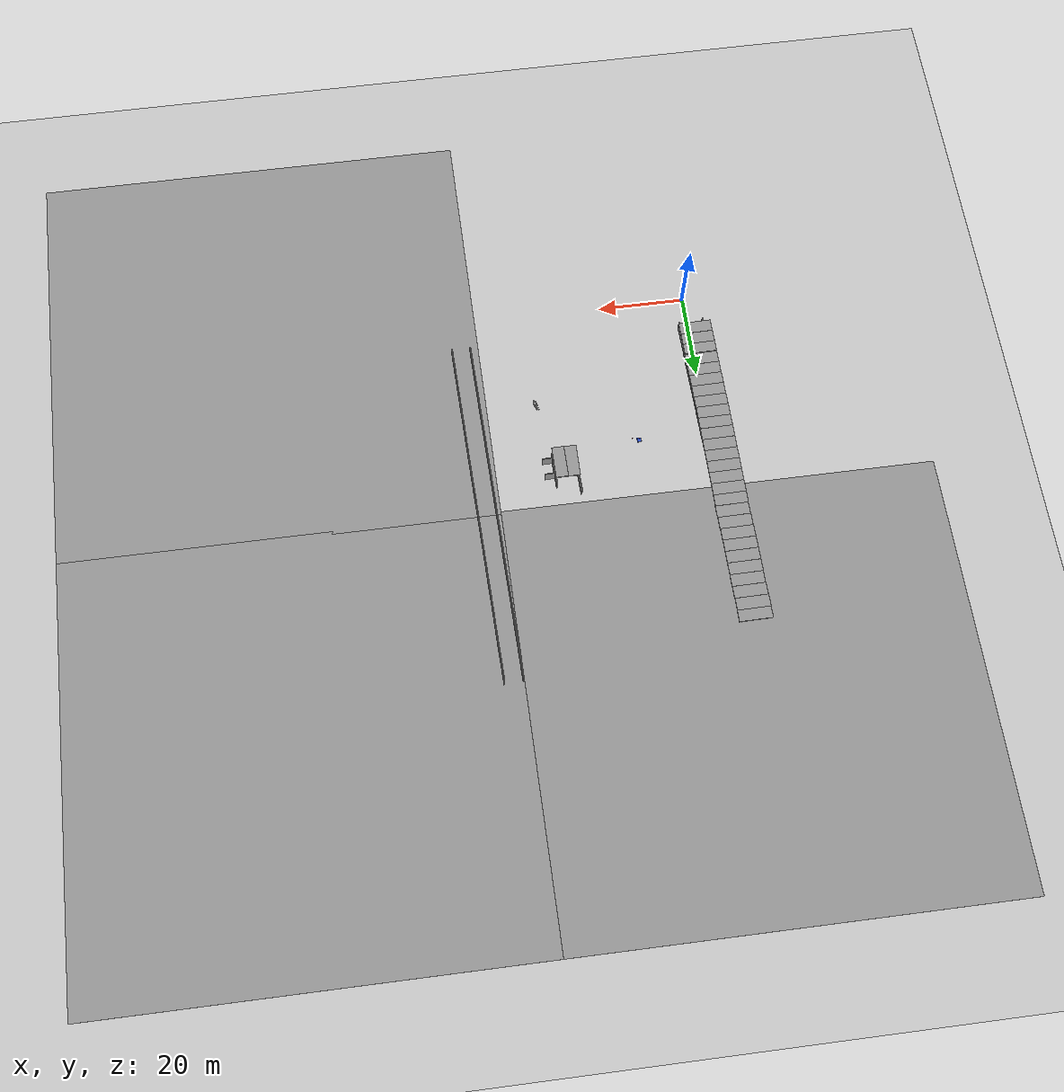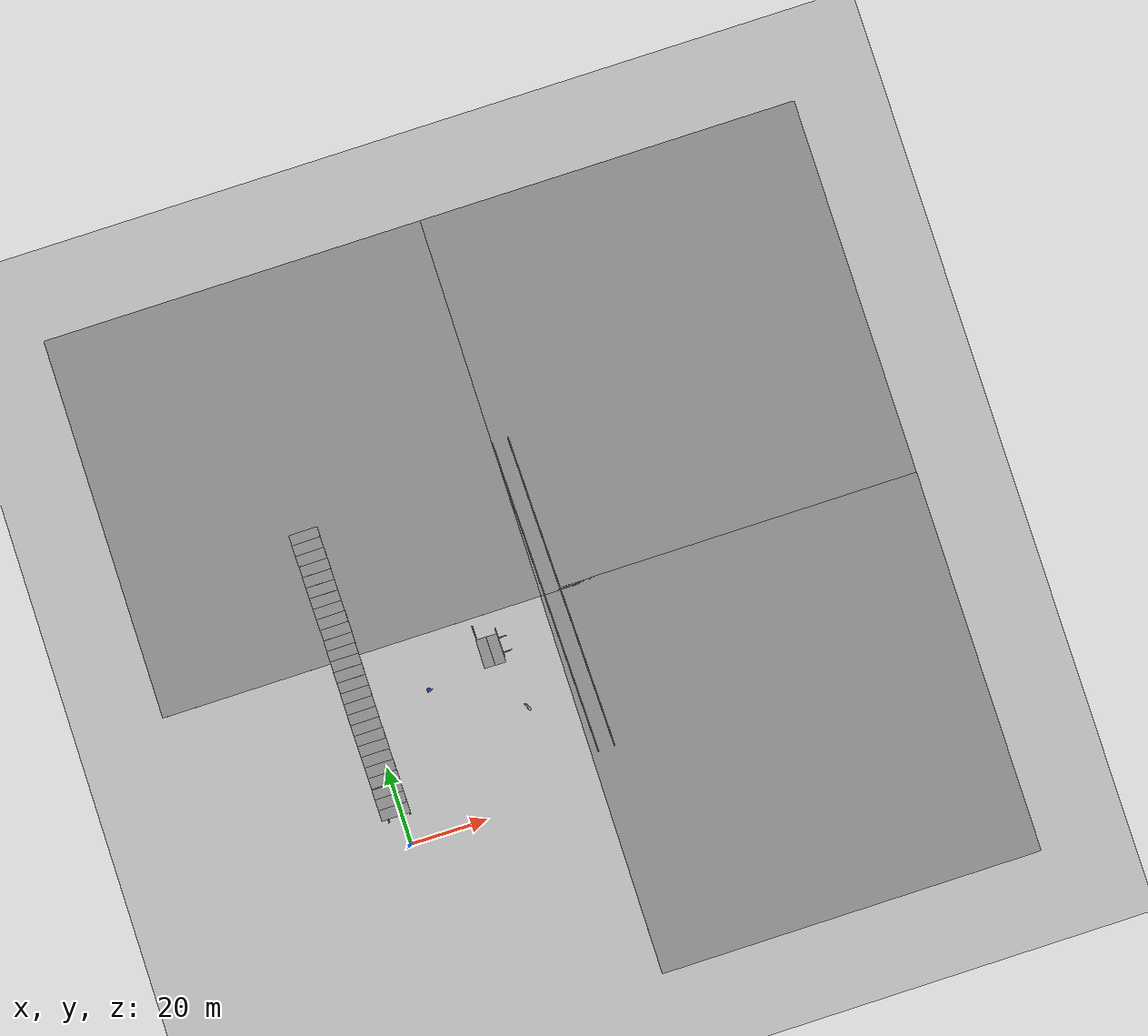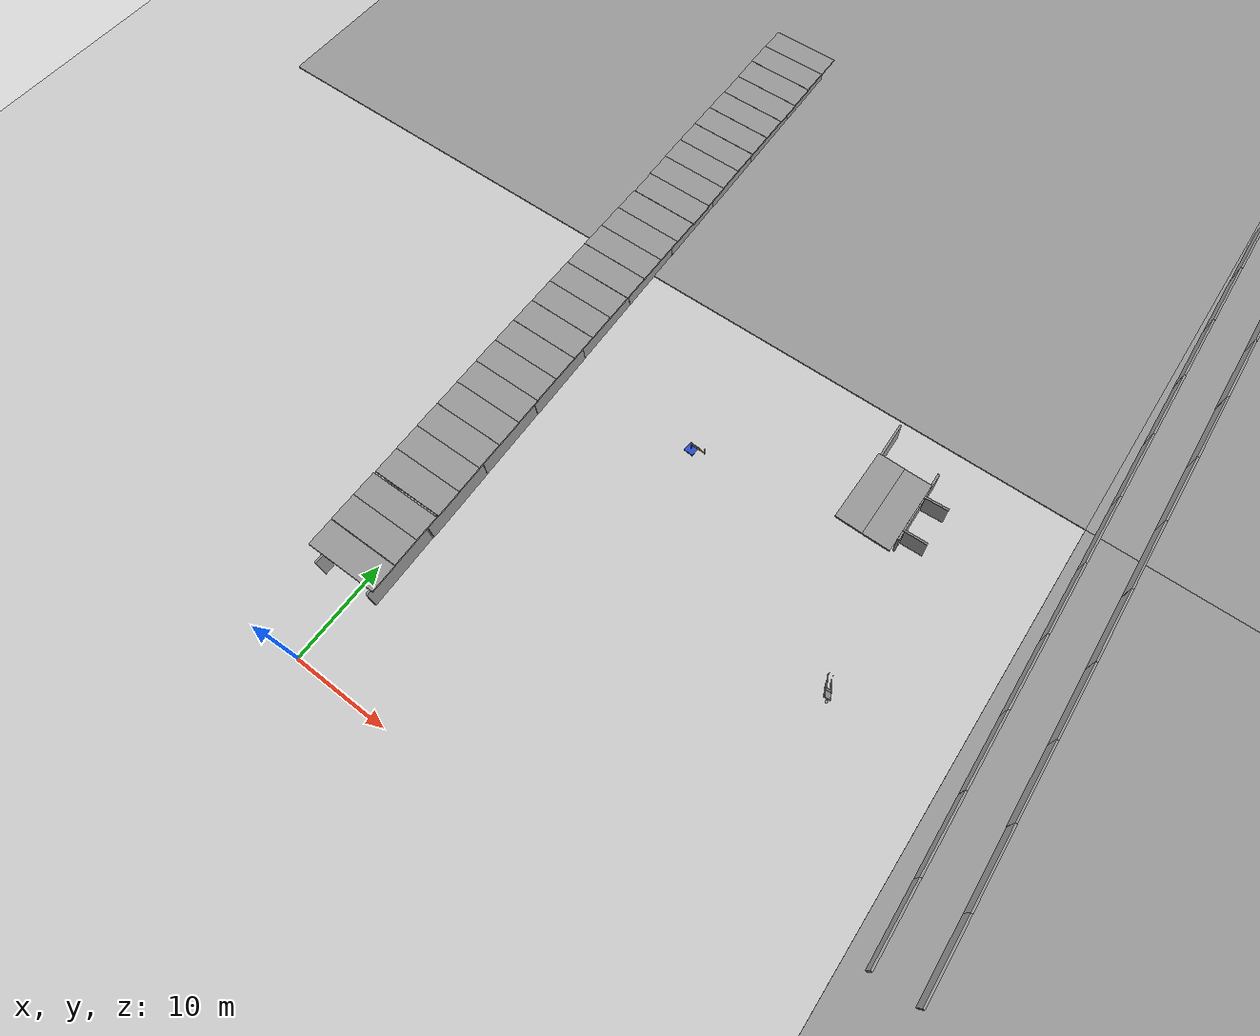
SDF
<sdf version="1.7">
 <world name="default">
  <light name="sun" type="directional">
   <pose>0 0 10 0 -0 0</pose>
   <diffuse>0.8 0.8 0.8 1</diffuse>
   <specular>0.2 0.2 0.2 1</specular>
   <attenuation>
    <range>1000</range>
    <constant>0.9</constant>
    <linear>0.01</linear>
    <quadratic>0.001</quadratic>
   </attenuation>
   <direction>-0.5 0.1 -0.9</direction>
   <spot><inner_angle>0</inner_angle><outer_angle>0</outer_angle><falloff>0</falloff></spot>
  </light>
  <model name="ground_plane">
   <static>1</static>
   <link name="link">
    <collision name="collision">
     <geometry><plane><normal>0 0 1</normal><size>100 100</size></plane></geometry>
     <surface><friction><ode><mu>100</mu><mu2>50</mu2></ode></friction></surface>
    </collision>
    <visual name="visual">
     <cast_shadows>0</cast_shadows>
     <geometry><plane><normal>0 0 1</normal><size>100 100</size></plane></geometry>
     <material>
      <script><uri>file://media/materials/scripts/gazebo.material</uri><name>Gazebo/Grey</name></script>
     </material>
    </visual>
   </link>
  </model>
  <gravity>0 0 -9.8</gravity>
  <magnetic_field>6e-06 2.3e-05 -4.2e-05</magnetic_field>
  <atmosphere type="adiabatic"/>
  <physics type="ode">
   <max_step_size>0.001</max_step_size>
   <real_time_factor>1</real_time_factor>
   <real_time_update_rate>1000</real_time_update_rate>
  </physics>
  <scene><ambient>0.4 0.4 0.4 1</ambient><background>0.7 0.7 0.7 1</background><shadows>1</shadows></scene>
  <spherical_coordinates>
   <surface_model>EARTH_WGS84</surface_model>
   <latitude_deg>0</latitude_deg>
   <longitude_deg>0</longitude_deg>
   <elevation>0</elevation>
   <heading_deg>0</heading_deg>
  </spherical_coordinates>
  <model name="ground_plane_0">
   <static>1</static>
   <link name="link">
    <collision name="collision">
     <geometry><plane><normal>0 0 1</normal><size>100 100</size></plane></geometry>
     <surface><friction><ode><mu>100</mu><mu2>50</mu2></ode></friction></surface>
    </collision>
    <visual name="visual">
     <cast_shadows>0</cast_shadows>
     <geometry><plane><normal>0 0 1</normal><size>100 100</size></plane></geometry>
     <material>
      <script><uri>file://media/materials/scripts/gazebo.material</uri><name>Gazebo/Grey</name></script>
     </material>
    </visual>
   </link>
   <pose>99.9426 -0.056054 0 0 -0 0</pose>
  </model>
  <model name="ground_plane_1">
   <static>1</static>
   <link name="link">
    <collision name="collision">
     <geometry><plane><normal>0 0 1</normal><size>100 100</size></plane></geometry>
     <surface><friction><ode><mu>100</mu><mu2>50</mu2></ode></friction></surface>
    </collision>
    <visual name="visual">
     <cast_shadows>0</cast_shadows>
     <geometry><plane><normal>0 0 1</normal><size>100 100</size></plane></geometry>
     <material>
      <script><uri>file://media/materials/scripts/gazebo.material</uri><name>Gazebo/Grey</name></script>
     </material>
    </visual>
   </link>
   <pose>0.099958 99.2729 0 0 -0 0</pose>
  </model>
  <model name="ground_plane_2">
   <static>1</static>
   <link name="link">
    <collision name="collision">
     <geometry><plane><normal>0 0 1</normal><size>100 100</size></plane></geometry>
     <surface><friction><ode><mu>100</mu><mu2>50</mu2></ode></friction></surface>
    </collision>
    <visual name="visual">
     <cast_shadows>0</cast_shadows>
     <geometry><plane><normal>0 0 1</normal><size>100 100</size></plane></geometry>
     <material>
      <script><uri>file://media/materials/scripts/gazebo.material</uri><name>Gazebo/Grey</name></script>
     </material>
    </visual>
   </link>
   <pose>99.9233 99.2771 0 0 -0 0</pose>
  </model>
  <model name="grey_wall">
   <static>1</static>
   <link name="link">
    <pose>0 0 1.4 0 -0 0</pose>
    <collision name="collision"><geometry><box><size>7.5 0.2 2.8</size></box></geometry></collision>
    <visual name="visual">
     <cast_shadows>0</cast_shadows>
     <geometry><box><size>7.5 0.2 2.8</size></box></geometry>
     <material>
      <script>
       <uri>model://grey_wall/materials/scripts</uri>
       <uri>model://grey_wall/materials/textures</uri>
       <name>vrc/grey_wall</name>
      </script>
     </material>
    </visual>
   </link>
   <pose>-3.89517 25.7087 0 0 -0 1.59137</pose>
  </model>
  <model name="grey_wall_clone">
   <static>1</static>
   <link name="link">
    <pose>0 0 1.4 0 -0 0</pose>
    <collision name="collision"><geometry><box><size>7.5 0.2 2.8</size></box></geometry></collision>
    <visual name="visual">
     <cast_shadows>0</cast_shadows>
     <geometry><box><size>7.5 0.2 2.8</size></box></geometry>
     <material>
      <script>
       <uri>model://grey_wall/materials/scripts</uri>
       <uri>model://grey_wall/materials/textures</uri>
       <name>vrc/grey_wall</name>
      </script>
     </material>
    </visual>
   </link>
   <pose>-3.75529 18.2122 0 0 -0 1.59137</pose>
  </model>
  <model name="grey_wall_clone_0">
   <static>1</static>
   <link name="link">
    <pose>0 0 1.4 0 -0 0</pose>
    <collision name="collision"><geometry><box><size>7.5 0.2 2.8</size></box></geometry></collision>
    <visual name="visual">
     <cast_shadows>0</cast_shadows>
     <geometry><box><size>7.5 0.2 2.8</size></box></geometry>
     <material>
      <script>
       <uri>model://grey_wall/materials/scripts</uri>
       <uri>model://grey_wall/materials/textures</uri>
       <name>vrc/grey_wall</name>
      </script>
     </material>
    </visual>
   </link>
   <pose>-3.568 10.6118 0 0 -0 1.59137</pose>
  </model>
  <model name="grey_wall_clone_2">
   <static>1</static>
   <link name="link">
    <pose>0 0 1.4 0 -0 0</pose>
    <collision name="collision"><geometry><box><size>7.5 0.2 2.8</size></box></geometry></collision>
    <visual name="visual">
     <cast_shadows>0</cast_shadows>
     <geometry><box><size>7.5 0.2 2.8</size></box></geometry>
     <material>
      <script>
       <uri>model://grey_wall/materials/scripts</uri>
       <uri>model://grey_wall/materials/textures</uri>
       <name>vrc/grey_wall</name>
      </script>
     </material>
    </visual>
   </link>
   <pose>-4.04207 33.233 0 0 -0 1.59137</pose>
  </model>
  <model name="grey_wall_clone_3">
   <static>1</static>
   <link name="link">
    <pose>0 0 1.4 0 -0 0</pose>
    <collision name="collision"><geometry><box><size>7.5 0.2 2.8</size></box></geometry></collision>
    <visual name="visual">
     <cast_shadows>0</cast_shadows>
     <geometry><box><size>7.5 0.2 2.8</size></box></geometry>
     <material>
      <script>
       <uri>model://grey_wall/materials/scripts</uri>
       <uri>model://grey_wall/materials/textures</uri>
       <name>vrc/grey_wall</name>
      </script>
     </material>
    </visual>
   </link>
   <pose>-4.14392 40.7338 0 0 -0 1.59137</pose>
  </model>
  <model name="grey_wall_clone_4">
   <static>1</static>
   <link name="link">
    <pose>0 0 1.4 0 -0 0</pose>
    <collision name="collision"><geometry><box><size>7.5 0.2 2.8</size></box></geometry></collision>
    <visual name="visual">
     <cast_shadows>0</cast_shadows>
     <geometry><box><size>7.5 0.2 2.8</size></box></geometry>
     <material>
      <script>
       <uri>model://grey_wall/materials/scripts</uri>
       <uri>model://grey_wall/materials/textures</uri>
       <name>vrc/grey_wall</name>
      </script>
     </material>
    </visual>
   </link>
   <pose>1.49292 41.2073 0.00396 0 -0 1.59137</pose>
  </model>
  <model name="grey_wall_clone_5">
   <static>1</static>
   <link name="link">
    <pose>0 0 1.4 0 -0 0</pose>
    <collision name="collision"><geometry><box><size>7.5 0.2 2.8</size></box></geometry></collision>
    <visual name="visual">
     <cast_shadows>0</cast_shadows>
     <geometry><box><size>7.5 0.2 2.8</size></box></geometry>
     <material>
      <script>
       <uri>model://grey_wall/materials/scripts</uri>
       <uri>model://grey_wall/materials/textures</uri>
       <name>vrc/grey_wall</name>
      </script>
     </material>
    </visual>
   </link>
   <pose>1.66348 33.6936 0 0 -0 1.59137</pose>
  </model>
  <model name="grey_wall_clone_6">
   <static>1</static>
   <link name="link">
    <pose>0 0 1.4 0 -0 0</pose>
    <collision name="collision"><geometry><box><size>7.5 0.2 2.8</size></box></geometry></collision>
    <visual name="visual">
     <cast_shadows>0</cast_shadows>
     <geometry><box><size>7.5 0.2 2.8</size></box></geometry>
     <material>
      <script>
       <uri>model://grey_wall/materials/scripts</uri>
       <uri>model://grey_wall/materials/textures</uri>
       <name>vrc/grey_wall</name>
      </script>
     </material>
    </visual>
   </link>
   <pose>1.78721 26.2071 0 0 -0 1.59137</pose>
  </model>
  <model name="grey_wall_clone_7">
   <static>1</static>
   <link name="link">
    <pose>0 0 1.4 0 -0 0</pose>
    <collision name="collision"><geometry><box><size>7.5 0.2 2.8</size></box></geometry></collision>
    <visual name="visual">
     <cast_shadows>0</cast_shadows>
     <geometry><box><size>7.5 0.2 2.8</size></box></geometry>
     <material>
      <script>
       <uri>model://grey_wall/materials/scripts</uri>
       <uri>model://grey_wall/materials/textures</uri>
       <name>vrc/grey_wall</name>
      </script>
     </material>
    </visual>
   </link>
   <pose>1.95483 18.6741 0 0 -0 1.59137</pose>
  </model>
  <model name="grey_wall_clone_8">
   <static>1</static>
   <link name="link">
    <pose>0 0 1.4 0 -0 0</pose>
    <collision name="collision"><geometry><box><size>7.5 0.2 2.8</size></box></geometry></collision>
    <visual name="visual">
     <cast_shadows>0</cast_shadows>
     <geometry><box><size>7.5 0.2 2.8</size></box></geometry>
     <material>
      <script>
       <uri>model://grey_wall/materials/scripts</uri>
       <uri>model://grey_wall/materials/textures</uri>
       <name>vrc/grey_wall</name>
      </script>
     </material>
    </visual>
   </link>
   <pose>2.04448 11.0446 0 0 -0 1.59137</pose>
  </model>
  <model name="grey_wall_clone_9">
   <static>1</static>
   <link name="link">
    <pose>0 0 1.4 0 -0 0</pose>
    <collision name="collision"><geometry><box><size>7.5 0.2 2.8</size></box></geometry></collision>
    <visual name="visual">
     <cast_shadows>0</cast_shadows>
     <geometry><box><size>7.5 0.2 2.8</size></box></geometry>
     <material>
      <script>
       <uri>model://grey_wall/materials/scripts</uri>
       <uri>model://grey_wall/materials/textures</uri>
       <name>vrc/grey_wall</name>
      </script>
     </material>
    </visual>
   </link>
   <pose>-4.3247 48.1948 0 0 -0 1.59137</pose>
  </model>
  <model name="grey_wall_clone_10">
   <static>1</static>
   <link name="link">
    <pose>0 0 1.4 0 -0 0</pose>
    <collision name="collision"><geometry><box><size>7.5 0.2 2.8</size></box></geometry></collision>
    <visual name="visual">
     <cast_shadows>0</cast_shadows>
     <geometry><box><size>7.5 0.2 2.8</size></box></geometry>
     <material>
      <script>
       <uri>model://grey_wall/materials/scripts</uri>
       <uri>model://grey_wall/materials/textures</uri>
       <name>vrc/grey_wall</name>
      </script>
     </material>
    </visual>
   </link>
   <pose>1.34127 48.72 0 0 -0 1.59137</pose>
  </model>
  <model name="grey_wall_clone_1">
   <static>1</static>
   <link name="link">
    <pose>0 0 1.4 0 -0 0</pose>
    <collision name="collision"><geometry><box><size>7.5 0.2 2.8</size></box></geometry></collision>
    <visual name="visual">
     <cast_shadows>0</cast_shadows>
     <geometry><box><size>7.5 0.2 2.8</size></box></geometry>
     <material>
      <script>
       <uri>model://grey_wall/materials/scripts</uri>
       <uri>model://grey_wall/materials/textures</uri>
       <name>vrc/grey_wall</name>
      </script>
     </material>
    </visual>
   </link>
   <pose>-1.62331 49.7018 2.86115 1.57041 -0.013654 -3.13613</pose>
  </model>
  <model name="grey_wall_clone_1_clone">
   <static>1</static>
   <link name="link">
    <pose>0 0 1.4 0 -0 0</pose>
    <collision name="collision"><geometry><box><size>7.5 0.2 2.8</size></box></geometry></collision>
    <visual name="visual">
     <cast_shadows>0</cast_shadows>
     <geometry><box><size>7.5 0.2 2.8</size></box></geometry>
     <material>
      <script>
       <uri>model://grey_wall/materials/scripts</uri>
       <uri>model://grey_wall/materials/textures</uri>
       <name>vrc/grey_wall</name>
      </script>
     </material>
    </visual>
   </link>
   <pose>-1.62327 46.905 2.86115 1.57041 -0.013654 -3.13613</pose>
  </model>
  <model name="grey_wall_clone_1_clone_0">
   <static>1</static>
   <link name="link">
    <pose>0 0 1.4 0 -0 0</pose>
    <collision name="collision"><geometry><box><size>7.5 0.2 2.8</size></box></geometry></collision>
    <visual name="visual">
     <cast_shadows>0</cast_shadows>
     <geometry><box><size>7.5 0.2 2.8</size></box></geometry>
     <material>
      <script>
       <uri>model://grey_wall/materials/scripts</uri>
       <uri>model://grey_wall/materials/textures</uri>
       <name>vrc/grey_wall</name>
      </script>
     </material>
    </visual>
   </link>
   <pose>-1.61773 44.0989 2.86115 1.57041 -0.013654 -3.13613</pose>
  </model>
  <model name="grey_wall_clone_1_clone_1">
   <static>1</static>
   <link name="link">
    <pose>0 0 1.4 0 -0 0</pose>
    <collision name="collision"><geometry><box><size>7.5 0.2 2.8</size></box></geometry></collision>
    <visual name="visual">
     <cast_shadows>0</cast_shadows>
     <geometry><box><size>7.5 0.2 2.8</size></box></geometry>
     <material>
      <script>
       <uri>model://grey_wall/materials/scripts</uri>
       <uri>model://grey_wall/materials/textures</uri>
       <name>vrc/grey_wall</name>
      </script>
     </material>
    </visual>
   </link>
   <pose>-1.61264 41.2893 2.86115 1.57041 -0.013654 -3.13613</pose>
  </model>
  <model name="grey_wall_clone_1_clone_2">
   <static>1</static>
   <link name="link">
    <pose>0 0 1.4 0 -0 0</pose>
    <collision name="collision"><geometry><box><size>7.5 0.2 2.8</size></box></geometry></collision>
    <visual name="visual">
     <cast_shadows>0</cast_shadows>
     <geometry><box><size>7.5 0.2 2.8</size></box></geometry>
     <material>
      <script>
       <uri>model://grey_wall/materials/scripts</uri>
       <uri>model://grey_wall/materials/textures</uri>
       <name>vrc/grey_wall</name>
      </script>
     </material>
    </visual>
   </link>
   <pose>-1.61138 38.525 2.86115 1.57041 -0.013654 -3.13613</pose>
  </model>
  <model name="grey_wall_clone_1_clone_3">
   <static>1</static>
   <link name="link">
    <pose>0 0 1.4 0 -0 0</pose>
    <collision name="collision"><geometry><box><size>7.5 0.2 2.8</size></box></geometry></collision>
    <visual name="visual">
     <cast_shadows>0</cast_shadows>
     <geometry><box><size>7.5 0.2 2.8</size></box></geometry>
     <material>
      <script>
       <uri>model://grey_wall/materials/scripts</uri>
       <uri>model://grey_wall/materials/textures</uri>
       <name>vrc/grey_wall</name>
      </script>
     </material>
    </visual>
   </link>
   <pose>-1.60564 35.7185 2.86115 1.57041 -0.013654 -3.13613</pose>
  </model>
  <model name="grey_wall_clone_1_clone_4">
   <static>1</static>
   <link name="link">
    <pose>0 0 1.4 0 -0 0</pose>
    <collision name="collision"><geometry><box><size>7.5 0.2 2.8</size></box></geometry></collision>
    <visual name="visual">
     <cast_shadows>0</cast_shadows>
     <geometry><box><size>7.5 0.2 2.8</size></box></geometry>
     <material>
      <script>
       <uri>model://grey_wall/materials/scripts</uri>
       <uri>model://grey_wall/materials/textures</uri>
       <name>vrc/grey_wall</name>
      </script>
     </material>
    </visual>
   </link>
   <pose>-1.60116 32.9123 2.86115 1.57041 -0.013654 -3.13613</pose>
  </model>
  <model name="grey_wall_clone_1_clone_5">
   <static>1</static>
   <link name="link">
    <pose>0 0 1.4 0 -0 0</pose>
    <collision name="collision"><geometry><box><size>7.5 0.2 2.8</size></box></geometry></collision>
    <visual name="visual">
     <cast_shadows>0</cast_shadows>
     <geometry><box><size>7.5 0.2 2.8</size></box></geometry>
     <material>
      <script>
       <uri>model://grey_wall/materials/scripts</uri>
       <uri>model://grey_wall/materials/textures</uri>
       <name>vrc/grey_wall</name>
      </script>
     </material>
    </visual>
   </link>
   <pose>-1.59902 30.1513 2.86115 1.57041 -0.013654 -3.13613</pose>
  </model>
  <model name="grey_wall_clone_1_clone_6">
   <static>1</static>
   <link name="link">
    <pose>0 0 1.4 0 -0 0</pose>
    <collision name="collision"><geometry><box><size>7.5 0.2 2.8</size></box></geometry></collision>
    <visual name="visual">
     <cast_shadows>0</cast_shadows>
     <geometry><box><size>7.5 0.2 2.8</size></box></geometry>
     <material>
      <script>
       <uri>model://grey_wall/materials/scripts</uri>
       <uri>model://grey_wall/materials/textures</uri>
       <name>vrc/grey_wall</name>
      </script>
     </material>
    </visual>
   </link>
   <pose>-1.54915 27.3506 2.86115 1.57041 -0.013654 -3.13613</pose>
  </model>
  <model name="grey_wall_clone_1_clone_7">
   <static>1</static>
   <link name="link">
    <pose>0 0 1.4 0 -0 0</pose>
    <collision name="collision"><geometry><box><size>7.5 0.2 2.8</size></box></geometry></collision>
    <visual name="visual">
     <cast_shadows>0</cast_shadows>
     <geometry><box><size>7.5 0.2 2.8</size></box></geometry>
     <material>
      <script>
       <uri>model://grey_wall/materials/scripts</uri>
       <uri>model://grey_wall/materials/textures</uri>
       <name>vrc/grey_wall</name>
      </script>
     </material>
    </visual>
   </link>
   <pose>-1.50276 24.5932 2.86115 1.57041 -0.013654 -3.13613</pose>
  </model>
  <model name="grey_wall_clone_1_clone_8">
   <static>1</static>
   <link name="link">
    <pose>0 0 1.4 0 -0 0</pose>
    <collision name="collision"><geometry><box><size>7.5 0.2 2.8</size></box></geometry></collision>
    <visual name="visual">
     <cast_shadows>0</cast_shadows>
     <geometry><box><size>7.5 0.2 2.8</size></box></geometry>
     <material>
      <script>
       <uri>model://grey_wall/materials/scripts</uri>
       <uri>model://grey_wall/materials/textures</uri>
       <name>vrc/grey_wall</name>
      </script>
     </material>
    </visual>
   </link>
   <pose>-1.49738 21.7908 2.86115 1.57041 -0.013654 -3.13613</pose>
  </model>
  <model name="grey_wall_clone_1_clone_9">
   <static>1</static>
   <link name="link">
    <pose>0 0 1.4 0 -0 0</pose>
    <collision name="collision"><geometry><box><size>7.5 0.2 2.8</size></box></geometry></collision>
    <visual name="visual">
     <cast_shadows>0</cast_shadows>
     <geometry><box><size>7.5 0.2 2.8</size></box></geometry>
     <material>
      <script>
       <uri>model://grey_wall/materials/scripts</uri>
       <uri>model://grey_wall/materials/textures</uri>
       <name>vrc/grey_wall</name>
      </script>
     </material>
    </visual>
   </link>
   <pose>-1.44771 18.9914 2.86115 1.57041 -0.013654 -3.13613</pose>
  </model>
  <model name="grey_wall_clone_1_clone_10">
   <static>1</static>
   <link name="link">
    <pose>0 0 1.4 0 -0 0</pose>
    <collision name="collision"><geometry><box><size>7.5 0.2 2.8</size></box></geometry></collision>
    <visual name="visual">
     <cast_shadows>0</cast_shadows>
     <geometry><box><size>7.5 0.2 2.8</size></box></geometry>
     <material>
      <script>
       <uri>model://grey_wall/materials/scripts</uri>
       <uri>model://grey_wall/materials/textures</uri>
       <name>vrc/grey_wall</name>
      </script>
     </material>
    </visual>
   </link>
   <pose>-1.39742 16.193 2.86115 1.57041 -0.013654 -3.13613</pose>
  </model>
  <model name="grey_wall_clone_1_clone_11">
   <static>1</static>
   <link name="link">
    <pose>0 0 1.4 0 -0 0</pose>
    <collision name="collision"><geometry><box><size>7.5 0.2 2.8</size></box></geometry></collision>
    <visual name="visual">
     <cast_shadows>0</cast_shadows>
     <geometry><box><size>7.5 0.2 2.8</size></box></geometry>
     <material>
      <script>
       <uri>model://grey_wall/materials/scripts</uri>
       <uri>model://grey_wall/materials/textures</uri>
       <name>vrc/grey_wall</name>
      </script>
     </material>
    </visual>
   </link>
   <pose>-1.43252 13.2189 2.86115 1.57041 -0.013654 -3.13613</pose>
  </model>
  <model name="grey_wall_clone_1_clone_12">
   <static>1</static>
   <link name="link">
    <pose>0 0 1.4 0 -0 0</pose>
    <collision name="collision"><geometry><box><size>7.5 0.2 2.8</size></box></geometry></collision>
    <visual name="visual">
     <cast_shadows>0</cast_shadows>
     <geometry><box><size>7.5 0.2 2.8</size></box></geometry>
     <material>
      <script>
       <uri>model://grey_wall/materials/scripts</uri>
       <uri>model://grey_wall/materials/textures</uri>
       <name>vrc/grey_wall</name>
      </script>
     </material>
    </visual>
   </link>
   <pose>-1.40757 10.6247 2.86115 1.57041 -0.013654 -3.13613</pose>
  </model>
  <model name="grey_wall_clone_1_clone_13">
   <static>1</static>
   <link name="link">
    <pose>0 0 1.4 0 -0 0</pose>
    <collision name="collision"><geometry><box><size>7.5 0.2 2.8</size></box></geometry></collision>
    <visual name="visual">
     <cast_shadows>0</cast_shadows>
     <geometry><box><size>7.5 0.2 2.8</size></box></geometry>
     <material>
      <script>
       <uri>model://grey_wall/materials/scripts</uri>
       <uri>model://grey_wall/materials/textures</uri>
       <name>vrc/grey_wall</name>
      </script>
     </material>
    </visual>
   </link>
   <pose>-1.35278 7.78526 2.86115 1.57041 -0.013654 -3.13613</pose>
  </model>
  <model name="grey_wall_clone_9_clone">
   <static>1</static>
   <link name="link">
    <pose>0 0 1.4 0 -0 0</pose>
    <collision name="collision"><geometry><box><size>7.5 0.2 2.8</size></box></geometry></collision>
    <visual name="visual">
     <cast_shadows>0</cast_shadows>
     <geometry><box><size>7.5 0.2 2.8</size></box></geometry>
     <material>
      <script>
       <uri>model://grey_wall/materials/scripts</uri>
       <uri>model://grey_wall/materials/textures</uri>
       <name>vrc/grey_wall</name>
      </script>
     </material>
    </visual>
   </link>
   <pose>-4.44529 55.7221 0 0 -0 1.59137</pose>
  </model>
  <model name="grey_wall_clone_9_clone_clone">
   <static>1</static>
   <link name="link">
    <pose>0 0 1.4 0 -0 0</pose>
    <collision name="collision"><geometry><box><size>7.5 0.2 2.8</size></box></geometry></collision>
    <visual name="visual">
     <cast_shadows>0</cast_shadows>
     <geometry><box><size>7.5 0.2 2.8</size></box></geometry>
     <material>
      <script>
       <uri>model://grey_wall/materials/scripts</uri>
       <uri>model://grey_wall/materials/textures</uri>
       <name>vrc/grey_wall</name>
      </script>
     </material>
    </visual>
   </link>
   <pose>-4.59593 63.2204 0 0 -0 1.59137</pose>
  </model>
  <model name="grey_wall_clone_9_clone_clone_0">
   <static>1</static>
   <link name="link">
    <pose>0 0 1.4 0 -0 0</pose>
    <collision name="collision"><geometry><box><size>7.5 0.2 2.8</size></box></geometry></collision>
    <visual name="visual">
     <cast_shadows>0</cast_shadows>
     <geometry><box><size>7.5 0.2 2.8</size></box></geometry>
     <material>
      <script>
       <uri>model://grey_wall/materials/scripts</uri>
       <uri>model://grey_wall/materials/textures</uri>
       <name>vrc/grey_wall</name>
      </script>
     </material>
    </visual>
   </link>
   <pose>-4.73317 70.6375 0 0 -0 1.59137</pose>
  </model>
  <model name="grey_wall_clone_9_clone_clone_1">
   <static>1</static>
   <link name="link">
    <pose>0 0 1.4 0 -0 0</pose>
    <collision name="collision"><geometry><box><size>7.5 0.2 2.8</size></box></geometry></collision>
    <visual name="visual">
     <cast_shadows>0</cast_shadows>
     <geometry><box><size>7.5 0.2 2.8</size></box></geometry>
     <material>
      <script>
       <uri>model://grey_wall/materials/scripts</uri>
       <uri>model://grey_wall/materials/textures</uri>
       <name>vrc/grey_wall</name>
      </script>
     </material>
    </visual>
   </link>
   <pose>-4.88662 78.082 0 0 -0 1.59137</pose>
  </model>
  <model name="grey_wall_clone_9_clone_clone_2">
   <static>1</static>
   <link name="link">
    <pose>0 0 1.4 0 -0 0</pose>
    <collision name="collision"><geometry><box><size>7.5 0.2 2.8</size></box></geometry></collision>
    <visual name="visual">
     <cast_shadows>0</cast_shadows>
     <geometry><box><size>7.5 0.2 2.8</size></box></geometry>
     <material>
      <script>
       <uri>model://grey_wall/materials/scripts</uri>
       <uri>model://grey_wall/materials/textures</uri>
       <name>vrc/grey_wall</name>
      </script>
     </material>
    </visual>
   </link>
   <pose>1.22426 56.209 0 0 -0 1.59137</pose>
  </model>
  <model name="grey_wall_clone_9_clone_clone_3">
   <static>1</static>
   <link name="link">
    <pose>0 0 1.4 0 -0 0</pose>
    <collision name="collision"><geometry><box><size>7.5 0.2 2.8</size></box></geometry></collision>
    <visual name="visual">
     <cast_shadows>0</cast_shadows>
     <geometry><box><size>7.5 0.2 2.8</size></box></geometry>
     <material>
      <script>
       <uri>model://grey_wall/materials/scripts</uri>
       <uri>model://grey_wall/materials/textures</uri>
       <name>vrc/grey_wall</name>
      </script>
     </material>
    </visual>
   </link>
   <pose>1.11942 63.7229 0 0 -0 1.59137</pose>
  </model>
  <model name="grey_wall_clone_9_clone_clone_4">
   <static>1</static>
   <link name="link">
    <pose>0 0 1.4 0 -0 0</pose>
    <collision name="collision"><geometry><box><size>7.5 0.2 2.8</size></box></geometry></collision>
    <visual name="visual">
     <cast_shadows>0</cast_shadows>
     <geometry><box><size>7.5 0.2 2.8</size></box></geometry>
     <material>
      <script>
       <uri>model://grey_wall/materials/scripts</uri>
       <uri>model://grey_wall/materials/textures</uri>
       <name>vrc/grey_wall</name>
      </script>
     </material>
    </visual>
   </link>
   <pose>0.978804 71.2196 0 0 -0 1.59137</pose>
  </model>
  <model name="grey_wall_clone_9_clone_clone_5">
   <static>1</static>
   <link name="link">
    <pose>0 0 1.4 0 -0 0</pose>
    <collision name="collision"><geometry><box><size>7.5 0.2 2.8</size></box></geometry></collision>
    <visual name="visual">
     <cast_shadows>0</cast_shadows>
     <geometry><box><size>7.5 0.2 2.8</size></box></geometry>
     <material>
      <script>
       <uri>model://grey_wall/materials/scripts</uri>
       <uri>model://grey_wall/materials/textures</uri>
       <name>vrc/grey_wall</name>
      </script>
     </material>
    </visual>
   </link>
   <pose>0.844167 78.6971 0 0 -0 1.59137</pose>
  </model>
  <model name="grey_wall_clone_1_clone_14">
   <static>1</static>
   <link name="link">
    <pose>0 0 1.4 0 -0 0</pose>
    <collision name="collision"><geometry><box><size>7.5 0.2 2.8</size></box></geometry></collision>
    <visual name="visual">
     <cast_shadows>0</cast_shadows>
     <geometry><box><size>7.5 0.2 2.8</size></box></geometry>
     <material>
      <script>
       <uri>model://grey_wall/materials/scripts</uri>
       <uri>model://grey_wall/materials/textures</uri>
       <name>vrc/grey_wall</name>
      </script>
     </material>
    </visual>
   </link>
   <pose>-1.61513 52.435 2.86115 1.57041 -0.013654 -3.13613</pose>
  </model>
  <model name="grey_wall_clone_1_clone_15">
   <static>1</static>
   <link name="link">
    <pose>0 0 1.4 0 -0 0</pose>
    <collision name="collision"><geometry><box><size>7.5 0.2 2.8</size></box></geometry></collision>
    <visual name="visual">
     <cast_shadows>0</cast_shadows>
     <geometry><box><size>7.5 0.2 2.8</size></box></geometry>
     <material>
      <script>
       <uri>model://grey_wall/materials/scripts</uri>
       <uri>model://grey_wall/materials/textures</uri>
       <name>vrc/grey_wall</name>
      </script>
     </material>
    </visual>
   </link>
   <pose>-1.55498 55.2526 2.86115 1.57041 -0.013654 -3.13613</pose>
  </model>
  <model name="grey_wall_clone_1_clone_16">
   <static>1</static>
   <link name="link">
    <pose>0 0 1.4 0 -0 0</pose>
    <collision name="collision"><geometry><box><size>7.5 0.2 2.8</size></box></geometry></collision>
    <visual name="visual">
     <cast_shadows>0</cast_shadows>
     <geometry><box><size>7.5 0.2 2.8</size></box></geometry>
     <material>
      <script>
       <uri>model://grey_wall/materials/scripts</uri>
       <uri>model://grey_wall/materials/textures</uri>
       <name>vrc/grey_wall</name>
      </script>
     </material>
    </visual>
   </link>
   <pose>-1.64399 58.0484 2.86115 1.57041 -0.013654 -3.13613</pose>
  </model>
  <model name="grey_wall_clone_1_clone_17">
   <static>1</static>
   <link name="link">
    <pose>0 0 1.4 0 -0 0</pose>
    <collision name="collision"><geometry><box><size>7.5 0.2 2.8</size></box></geometry></collision>
    <visual name="visual">
     <cast_shadows>0</cast_shadows>
     <geometry><box><size>7.5 0.2 2.8</size></box></geometry>
     <material>
      <script>
       <uri>model://grey_wall/materials/scripts</uri>
       <uri>model://grey_wall/materials/textures</uri>
       <name>vrc/grey_wall</name>
      </script>
     </material>
    </visual>
   </link>
   <pose>-1.72464 60.8172 2.86115 1.57041 -0.013654 -3.13613</pose>
  </model>
  <model name="grey_wall_clone_1_clone_18">
   <static>1</static>
   <link name="link">
    <pose>0 0 1.4 0 -0 0</pose>
    <collision name="collision"><geometry><box><size>7.5 0.2 2.8</size></box></geometry></collision>
    <visual name="visual">
     <cast_shadows>0</cast_shadows>
     <geometry><box><size>7.5 0.2 2.8</size></box></geometry>
     <material>
      <script>
       <uri>model://grey_wall/materials/scripts</uri>
       <uri>model://grey_wall/materials/textures</uri>
       <name>vrc/grey_wall</name>
      </script>
     </material>
    </visual>
   </link>
   <pose>-1.75579 63.5811 2.86115 1.57041 -0.013654 -3.13613</pose>
  </model>
  <model name="grey_wall_clone_1_clone_19">
   <static>1</static>
   <link name="link">
    <pose>0 0 1.4 0 -0 0</pose>
    <collision name="collision"><geometry><box><size>7.5 0.2 2.8</size></box></geometry></collision>
    <visual name="visual">
     <cast_shadows>0</cast_shadows>
     <geometry><box><size>7.5 0.2 2.8</size></box></geometry>
     <material>
      <script>
       <uri>model://grey_wall/materials/scripts</uri>
       <uri>model://grey_wall/materials/textures</uri>
       <name>vrc/grey_wall</name>
      </script>
     </material>
    </visual>
   </link>
   <pose>-1.77945 66.3932 2.86115 1.57041 -0.013654 -3.13613</pose>
  </model>
  <model name="grey_wall_clone_1_clone_20">
   <static>1</static>
   <link name="link">
    <pose>0 0 1.4 0 -0 0</pose>
    <collision name="collision"><geometry><box><size>7.5 0.2 2.8</size></box></geometry></collision>
    <visual name="visual">
     <cast_shadows>0</cast_shadows>
     <geometry><box><size>7.5 0.2 2.8</size></box></geometry>
     <material>
      <script>
       <uri>model://grey_wall/materials/scripts</uri>
       <uri>model://grey_wall/materials/textures</uri>
       <name>vrc/grey_wall</name>
      </script>
     </material>
    </visual>
   </link>
   <pose>-1.80324 69.203 2.86115 1.57041 -0.013654 -3.13613</pose>
  </model>
  <model name="grey_wall_clone_1_clone_21">
   <static>1</static>
   <link name="link">
    <pose>0 0 1.4 0 -0 0</pose>
    <collision name="collision"><geometry><box><size>7.5 0.2 2.8</size></box></geometry></collision>
    <visual name="visual">
     <cast_shadows>0</cast_shadows>
     <geometry><box><size>7.5 0.2 2.8</size></box></geometry>
     <material>
      <script>
       <uri>model://grey_wall/materials/scripts</uri>
       <uri>model://grey_wall/materials/textures</uri>
       <name>vrc/grey_wall</name>
      </script>
     </material>
    </visual>
   </link>
   <pose>-1.77665 72.0123 2.86115 1.57041 -0.013654 -3.13613</pose>
  </model>
  <model name="grey_wall_clone_1_clone_22">
   <static>1</static>
   <link name="link">
    <pose>0 0 1.4 0 -0 0</pose>
    <collision name="collision"><geometry><box><size>7.5 0.2 2.8</size></box></geometry></collision>
    <visual name="visual">
     <cast_shadows>0</cast_shadows>
     <geometry><box><size>7.5 0.2 2.8</size></box></geometry>
     <material>
      <script>
       <uri>model://grey_wall/materials/scripts</uri>
       <uri>model://grey_wall/materials/textures</uri>
       <name>vrc/grey_wall</name>
      </script>
     </material>
    </visual>
   </link>
   <pose>-1.851 74.8205 2.86115 1.57041 -0.013654 -3.13613</pose>
  </model>
  <model name="grey_wall_clone_1_clone_23">
   <static>1</static>
   <link name="link">
    <pose>0 0 1.4 0 -0 0</pose>
    <collision name="collision"><geometry><box><size>7.5 0.2 2.8</size></box></geometry></collision>
    <visual name="visual">
     <cast_shadows>0</cast_shadows>
     <geometry><box><size>7.5 0.2 2.8</size></box></geometry>
     <material>
      <script>
       <uri>model://grey_wall/materials/scripts</uri>
       <uri>model://grey_wall/materials/textures</uri>
       <name>vrc/grey_wall</name>
      </script>
     </material>
    </visual>
   </link>
   <pose>-1.925 77.6301 2.86115 1.57041 -0.013654 -3.13613</pose>
  </model>
  <model name="grey_wall_clone_1_clone_24">
   <static>1</static>
   <link name="link">
    <pose>0 0 1.4 0 -0 0</pose>
    <collision name="collision"><geometry><box><size>7.5 0.2 2.8</size></box></geometry></collision>
    <visual name="visual">
     <cast_shadows>0</cast_shadows>
     <geometry><box><size>7.5 0.2 2.8</size></box></geometry>
     <material>
      <script>
       <uri>model://grey_wall/materials/scripts</uri>
       <uri>model://grey_wall/materials/textures</uri>
       <name>vrc/grey_wall</name>
      </script>
     </material>
    </visual>
   </link>
   <pose>-1.91233 80.3321 2.86115 1.57041 -0.013654 -3.13613</pose>
  </model>
  <model name="grey_wall_clone_8_clone">
   <static>1</static>
   <link name="link">
    <pose>0 0 1.4 0 -0 0</pose>
    <collision name="collision"><geometry><box><size>7.5 0.2 2.8</size></box></geometry></collision>
    <visual name="visual">
     <cast_shadows>0</cast_shadows>
     <geometry><box><size>7.5 0.2 2.8</size></box></geometry>
     <material>
      <script>
       <uri>model://grey_wall/materials/scripts</uri>
       <uri>model://grey_wall/materials/textures</uri>
       <name>vrc/grey_wall</name>
      </script>
     </material>
    </visual>
   </link>
   <pose>51.7575 11.454 0 0 -0 1.59137</pose>
  </model>
  <model name="grey_wall_clone_8_clone_0">
   <static>1</static>
   <link name="link">
    <pose>0 0 1.4 0 -0 0</pose>
    <collision name="collision"><geometry><box><size>7.5 0.2 2.8</size></box></geometry></collision>
    <visual name="visual">
     <cast_shadows>0</cast_shadows>
     <geometry><box><size>7.5 0.2 2.8</size></box></geometry>
     <material>
      <script>
       <uri>model://grey_wall/materials/scripts</uri>
       <uri>model://grey_wall/materials/textures</uri>
       <name>vrc/grey_wall</name>
      </script>
     </material>
    </visual>
   </link>
   <pose>51.6047 18.9221 0 0 -0 1.59137</pose>
  </model>
  <model name="grey_wall_clone_8_clone_1">
   <static>1</static>
   <link name="link">
    <pose>0 0 1.4 0 -0 0</pose>
    <collision name="collision"><geometry><box><size>7.5 0.2 2.8</size></box></geometry></collision>
    <visual name="visual">
     <cast_shadows>0</cast_shadows>
     <geometry><box><size>7.5 0.2 2.8</size></box></geometry>
     <material>
      <script>
       <uri>model://grey_wall/materials/scripts</uri>
       <uri>model://grey_wall/materials/textures</uri>
       <name>vrc/grey_wall</name>
      </script>
     </material>
    </visual>
   </link>
   <pose>51.4463 26.3961 0 0 -0 1.59137</pose>
  </model>
  <model name="grey_wall_clone_8_clone_2">
   <static>1</static>
   <link name="link">
    <pose>0 0 1.4 0 -0 0</pose>
    <collision name="collision"><geometry><box><size>7.5 0.2 2.8</size></box></geometry></collision>
    <visual name="visual">
     <cast_shadows>0</cast_shadows>
     <geometry><box><size>7.5 0.2 2.8</size></box></geometry>
     <material>
      <script>
       <uri>model://grey_wall/materials/scripts</uri>
       <uri>model://grey_wall/materials/textures</uri>
       <name>vrc/grey_wall</name>
      </script>
     </material>
    </visual>
   </link>
   <pose>51.2894 33.8539 0 0 -0 1.59137</pose>
  </model>
  <model name="grey_wall_clone_8_clone_3">
   <static>1</static>
   <link name="link">
    <pose>0 0 1.4 0 -0 0</pose>
    <collision name="collision"><geometry><box><size>7.5 0.2 2.8</size></box></geometry></collision>
    <visual name="visual">
     <cast_shadows>0</cast_shadows>
     <geometry><box><size>7.5 0.2 2.8</size></box></geometry>
     <material>
      <script>
       <uri>model://grey_wall/materials/scripts</uri>
       <uri>model://grey_wall/materials/textures</uri>
       <name>vrc/grey_wall</name>
      </script>
     </material>
    </visual>
   </link>
   <pose>51.1359 41.3367 0 0 -0 1.59137</pose>
  </model>
  <model name="grey_wall_clone_8_clone_4">
   <static>1</static>
   <link name="link">
    <pose>0 0 1.4 0 -0 0</pose>
    <collision name="collision"><geometry><box><size>7.5 0.2 2.8</size></box></geometry></collision>
    <visual name="visual">
     <cast_shadows>0</cast_shadows>
     <geometry><box><size>7.5 0.2 2.8</size></box></geometry>
     <material>
      <script>
       <uri>model://grey_wall/materials/scripts</uri>
       <uri>model://grey_wall/materials/textures</uri>
       <name>vrc/grey_wall</name>
      </script>
     </material>
    </visual>
   </link>
   <pose>50.99 48.8327 0 0 -0 1.59137</pose>
  </model>
  <model name="grey_wall_clone_8_clone_5">
   <static>1</static>
   <link name="link">
    <pose>0 0 1.4 0 -0 0</pose>
    <collision name="collision"><geometry><box><size>7.5 0.2 2.8</size></box></geometry></collision>
    <visual name="visual">
     <cast_shadows>0</cast_shadows>
     <geometry><box><size>7.5 0.2 2.8</size></box></geometry>
     <material>
      <script>
       <uri>model://grey_wall/materials/scripts</uri>
       <uri>model://grey_wall/materials/textures</uri>
       <name>vrc/grey_wall</name>
      </script>
     </material>
    </visual>
   </link>
   <pose>50.8329 56.2723 0 0 -0 1.59137</pose>
  </model>
  <model name="grey_wall_clone_8_clone_6">
   <static>1</static>
   <link name="link">
    <pose>0 0 1.4 0 -0 0</pose>
    <collision name="collision"><geometry><box><size>7.5 0.2 2.8</size></box></geometry></collision>
    <visual name="visual">
     <cast_shadows>0</cast_shadows>
     <geometry><box><size>7.5 0.2 2.8</size></box></geometry>
     <material>
      <script>
       <uri>model://grey_wall/materials/scripts</uri>
       <uri>model://grey_wall/materials/textures</uri>
       <name>vrc/grey_wall</name>
      </script>
     </material>
    </visual>
   </link>
   <pose>50.6922 63.7482 0 0 -0 1.59137</pose>
  </model>
  <model name="grey_wall_clone_8_clone_7">
   <static>1</static>
   <link name="link">
    <pose>0 0 1.4 0 -0 0</pose>
    <collision name="collision"><geometry><box><size>7.5 0.2 2.8</size></box></geometry></collision>
    <visual name="visual">
     <cast_shadows>0</cast_shadows>
     <geometry><box><size>7.5 0.2 2.8</size></box></geometry>
     <material>
      <script>
       <uri>model://grey_wall/materials/scripts</uri>
       <uri>model://grey_wall/materials/textures</uri>
       <name>vrc/grey_wall</name>
      </script>
     </material>
    </visual>
   </link>
   <pose>50.5227 71.2335 0 0 -0 1.59137</pose>
  </model>
  <model name="grey_wall_clone_8_clone_8">
   <static>1</static>
   <link name="link">
    <pose>0 0 1.4 0 -0 0</pose>
    <collision name="collision"><geometry><box><size>7.5 0.2 2.8</size></box></geometry></collision>
    <visual name="visual">
     <cast_shadows>0</cast_shadows>
     <geometry><box><size>7.5 0.2 2.8</size></box></geometry>
     <material>
      <script>
       <uri>model://grey_wall/materials/scripts</uri>
       <uri>model://grey_wall/materials/textures</uri>
       <name>vrc/grey_wall</name>
      </script>
     </material>
    </visual>
   </link>
   <pose>50.385 78.6478 0 0 -0 1.59137</pose>
  </model>
  <model name="grey_wall_clone_8_clone_9">
   <static>1</static>
   <link name="link">
    <pose>0 0 1.4 0 -0 0</pose>
    <collision name="collision"><geometry><box><size>7.5 0.2 2.8</size></box></geometry></collision>
    <visual name="visual">
     <cast_shadows>0</cast_shadows>
     <geometry><box><size>7.5 0.2 2.8</size></box></geometry>
     <material>
      <script>
       <uri>model://grey_wall/materials/scripts</uri>
       <uri>model://grey_wall/materials/textures</uri>
       <name>vrc/grey_wall</name>
      </script>
     </material>
    </visual>
   </link>
   <pose>50.2557 86.1318 0 0 -0 1.59137</pose>
  </model>
  <model name="grey_wall_clone_8_clone_10">
   <static>1</static>
   <link name="link">
    <pose>0 0 1.4 0 -0 0</pose>
    <collision name="collision"><geometry><box><size>7.5 0.2 2.8</size></box></geometry></collision>
    <visual name="visual">
     <cast_shadows>0</cast_shadows>
     <geometry><box><size>7.5 0.2 2.8</size></box></geometry>
     <material>
      <script>
       <uri>model://grey_wall/materials/scripts</uri>
       <uri>model://grey_wall/materials/textures</uri>
       <name>vrc/grey_wall</name>
      </script>
     </material>
    </visual>
   </link>
   <pose>56.0589 11.5382 0 0 -0 1.59137</pose>
  </model>
  <model name="grey_wall_clone_8_clone_11">
   <static>1</static>
   <link name="link">
    <pose>0 0 1.4 0 -0 0</pose>
    <collision name="collision"><geometry><box><size>7.5 0.2 2.8</size></box></geometry></collision>
    <visual name="visual">
     <cast_shadows>0</cast_shadows>
     <geometry><box><size>7.5 0.2 2.8</size></box></geometry>
     <material>
      <script>
       <uri>model://grey_wall/materials/scripts</uri>
       <uri>model://grey_wall/materials/textures</uri>
       <name>vrc/grey_wall</name>
      </script>
     </material>
    </visual>
   </link>
   <pose>55.9095 18.9862 0 0 -0 1.59137</pose>
  </model>
  <model name="grey_wall_clone_8_clone_12">
   <static>1</static>
   <link name="link">
    <pose>0 0 1.4 0 -0 0</pose>
    <collision name="collision"><geometry><box><size>7.5 0.2 2.8</size></box></geometry></collision>
    <visual name="visual">
     <cast_shadows>0</cast_shadows>
     <geometry><box><size>7.5 0.2 2.8</size></box></geometry>
     <material>
      <script>
       <uri>model://grey_wall/materials/scripts</uri>
       <uri>model://grey_wall/materials/textures</uri>
       <name>vrc/grey_wall</name>
      </script>
     </material>
    </visual>
   </link>
   <pose>55.7363 26.4782 0 0 -0 1.59137</pose>
  </model>
  <model name="grey_wall_clone_8_clone_13">
   <static>1</static>
   <link name="link">
    <pose>0 0 1.4 0 -0 0</pose>
    <collision name="collision"><geometry><box><size>7.5 0.2 2.8</size></box></geometry></collision>
    <visual name="visual">
     <cast_shadows>0</cast_shadows>
     <geometry><box><size>7.5 0.2 2.8</size></box></geometry>
     <material>
      <script>
       <uri>model://grey_wall/materials/scripts</uri>
       <uri>model://grey_wall/materials/textures</uri>
       <name>vrc/grey_wall</name>
      </script>
     </material>
    </visual>
   </link>
   <pose>55.5922 33.9518 0 0 -0 1.59137</pose>
  </model>
  <model name="grey_wall_clone_8_clone_14">
   <static>1</static>
   <link name="link">
    <pose>0 0 1.4 0 -0 0</pose>
    <collision name="collision"><geometry><box><size>7.5 0.2 2.8</size></box></geometry></collision>
    <visual name="visual">
     <cast_shadows>0</cast_shadows>
     <geometry><box><size>7.5 0.2 2.8</size></box></geometry>
     <material>
      <script>
       <uri>model://grey_wall/materials/scripts</uri>
       <uri>model://grey_wall/materials/textures</uri>
       <name>vrc/grey_wall</name>
      </script>
     </material>
    </visual>
   </link>
   <pose>55.4328 41.4616 0 0 -0 1.59137</pose>
  </model>
  <model name="grey_wall_clone_8_clone_15">
   <static>1</static>
   <link name="link">
    <pose>0 0 1.4 0 -0 0</pose>
    <collision name="collision"><geometry><box><size>7.5 0.2 2.8</size></box></geometry></collision>
    <visual name="visual">
     <cast_shadows>0</cast_shadows>
     <geometry><box><size>7.5 0.2 2.8</size></box></geometry>
     <material>
      <script>
       <uri>model://grey_wall/materials/scripts</uri>
       <uri>model://grey_wall/materials/textures</uri>
       <name>vrc/grey_wall</name>
      </script>
     </material>
    </visual>
   </link>
   <pose>55.2541 48.9677 0 0 -0 1.59137</pose>
  </model>
  <model name="grey_wall_clone_8_clone_16">
   <static>1</static>
   <link name="link">
    <pose>0 0 1.4 0 -0 0</pose>
    <collision name="collision"><geometry><box><size>7.5 0.2 2.8</size></box></geometry></collision>
    <visual name="visual">
     <cast_shadows>0</cast_shadows>
     <geometry><box><size>7.5 0.2 2.8</size></box></geometry>
     <material>
      <script>
       <uri>model://grey_wall/materials/scripts</uri>
       <uri>model://grey_wall/materials/textures</uri>
       <name>vrc/grey_wall</name>
      </script>
     </material>
    </visual>
   </link>
   <pose>55.096 56.4117 0 0 -0 1.59137</pose>
  </model>
  <model name="grey_wall_clone_8_clone_17">
   <static>1</static>
   <link name="link">
    <pose>0 0 1.4 0 -0 0</pose>
    <collision name="collision"><geometry><box><size>7.5 0.2 2.8</size></box></geometry></collision>
    <visual name="visual">
     <cast_shadows>0</cast_shadows>
     <geometry><box><size>7.5 0.2 2.8</size></box></geometry>
     <material>
      <script>
       <uri>model://grey_wall/materials/scripts</uri>
       <uri>model://grey_wall/materials/textures</uri>
       <name>vrc/grey_wall</name>
      </script>
     </material>
    </visual>
   </link>
   <pose>54.937 63.9085 0 0 -0 1.59137</pose>
  </model>
  <model name="grey_wall_clone_8_clone_18">
   <static>1</static>
   <link name="link">
    <pose>0 0 1.4 0 -0 0</pose>
    <collision name="collision"><geometry><box><size>7.5 0.2 2.8</size></box></geometry></collision>
    <visual name="visual">
     <cast_shadows>0</cast_shadows>
     <geometry><box><size>7.5 0.2 2.8</size></box></geometry>
     <material>
      <script>
       <uri>model://grey_wall/materials/scripts</uri>
       <uri>model://grey_wall/materials/textures</uri>
       <name>vrc/grey_wall</name>
      </script>
     </material>
    </visual>
   </link>
   <pose>54.7627 71.3613 0 0 -0 1.59137</pose>
  </model>
  <model name="grey_wall_clone_8_clone_19">
   <static>1</static>
   <link name="link">
    <pose>0 0 1.4 0 -0 0</pose>
    <collision name="collision"><geometry><box><size>7.5 0.2 2.8</size></box></geometry></collision>
    <visual name="visual">
     <cast_shadows>0</cast_shadows>
     <geometry><box><size>7.5 0.2 2.8</size></box></geometry>
     <material>
      <script>
       <uri>model://grey_wall/materials/scripts</uri>
       <uri>model://grey_wall/materials/textures</uri>
       <name>vrc/grey_wall</name>
      </script>
     </material>
    </visual>
   </link>
   <pose>54.6332 78.7954 0 0 -0 1.59137</pose>
  </model>
  <model name="grey_wall_clone_8_clone_20">
   <static>1</static>
   <link name="link">
    <pose>0 0 1.4 0 -0 0</pose>
    <collision name="collision"><geometry><box><size>7.5 0.2 2.8</size></box></geometry></collision>
    <visual name="visual">
     <cast_shadows>0</cast_shadows>
     <geometry><box><size>7.5 0.2 2.8</size></box></geometry>
     <material>
      <script>
       <uri>model://grey_wall/materials/scripts</uri>
       <uri>model://grey_wall/materials/textures</uri>
       <name>vrc/grey_wall</name>
      </script>
     </material>
    </visual>
   </link>
   <pose>54.457 86.2764 0 0 -0 1.59137</pose>
  </model>
  <model name="ragdoll">
   <pose>38.4237 23.7287 0.370639 0.952918 -0.912161 0.913459</pose>
   <link name="hip">
    <inertial>
     <inertia><ixx>0.1</ixx><ixy>0</ixy><ixz>0</ixz><iyy>0.1</iyy><iyz>0</iyz><izz>0.1</izz></inertia>
     <mass>10</mass>
    </inertial>
    <collision name="hip_geom">
     <pose>0 0 0.125 0 -0 0</pose>
     <geometry><box><size>0.1 0.5 0.25</size></box></geometry>
     <surface>
      <friction><ode><mu>-1</mu><mu2>-1</mu2><fdir1>0 0 0</fdir1><slip1>0</slip1><slip2>0</slip2></ode></friction>
      <bounce><restitution_coefficient>0</restitution_coefficient><threshold>100000</threshold></bounce>
      <contact>
       <ode>
        <soft_cfm>0</soft_cfm>
        <soft_erp>0.2</soft_erp>
        <kp>1e+12</kp>
        <kd>1</kd>
        <max_vel>0</max_vel>
        <min_depth>0.001</min_depth>
       </ode>
      </contact>
     </surface>
    </collision>
    <visual name="hip_geom_visual">
     <pose>0 0 0.125 0 -0 0</pose>
     <geometry><box><size>0.1 0.5 0.25</size></box></geometry>
    </visual>
    <gravity>0</gravity>
   </link>
   <link name="l_thigh_pan">
    <pose>0 0.22 0 0 -0 0</pose>
    <inertial>
     <inertia><ixx>0.01</ixx><ixy>0</ixy><ixz>0</ixz><iyy>0.01</iyy><iyz>0</iyz><izz>0.01</izz></inertia>
     <mass>1</mass>
    </inertial>
    <collision name="l_thigh_pan_geom">
     <pose>0 0 -0.03 0 -0 0</pose>
     <geometry><sphere><radius>0.06</radius></sphere></geometry>
     <surface>
      <friction><ode><mu>-1</mu><mu2>-1</mu2><fdir1>0 0 0</fdir1><slip1>0</slip1><slip2>0</slip2></ode></friction>
      <bounce><restitution_coefficient>0</restitution_coefficient><threshold>100000</threshold></bounce>
      <contact>
       <ode>
        <soft_cfm>0</soft_cfm>
        <soft_erp>0.2</soft_erp>
        <kp>1e+12</kp>
        <kd>1</kd>
        <max_vel>0</max_vel>
        <min_depth>0.001</min_depth>
       </ode>
      </contact>
     </surface>
    </collision>
    <visual name="l_thigh_pan_geom_visual">
     <pose>0 0 -0.03 0 -0 0</pose>
     <geometry><sphere><radius>0.06</radius></sphere></geometry>
    </visual>
    <gravity>0</gravity>
   </link>
   <link name="l_thigh_lift">
    <pose>0 0.22 0 0 -0 0</pose>
    <inertial>
     <inertia><ixx>0.05</ixx><ixy>0</ixy><ixz>0</ixz><iyy>0.05</iyy><iyz>0</iyz><izz>0.05</izz></inertia>
     <mass>5</mass>
    </inertial>
    <collision name="l_thigh_lift_geom">
     <pose>0 0 -0.35 0 -0 0</pose>
     <geometry><cylinder><radius>0.06</radius><length>0.7</length></cylinder></geometry>
     <surface>
      <friction><ode><mu>-1</mu><mu2>-1</mu2><fdir1>0 0 0</fdir1><slip1>0</slip1><slip2>0</slip2></ode></friction>
      <bounce><restitution_coefficient>0</restitution_coefficient><threshold>100000</threshold></bounce>
      <contact>
       <ode>
        <soft_cfm>0</soft_cfm>
        <soft_erp>0.2</soft_erp>
        <kp>1e+12</kp>
        <kd>1</kd>
        <max_vel>0</max_vel>
        <min_depth>0.001</min_depth>
       </ode>
      </contact>
     </surface>
    </collision>
    <visual name="l_thigh_lift_geom_visual">
     <pose>0 0 -0.35 0 -0 0</pose>
     <geometry><cylinder><radius>0.06</radius><length>0.7</length></cylinder></geometry>
    </visual>
    <gravity>0</gravity>
   </link>
   <link name="l_calf">
    <pose>0 0.22 -0.7 0 -0 0</pose>
    <inertial>
     <inertia><ixx>0.02</ixx><ixy>0</ixy><ixz>0</ixz><iyy>0.02</iyy><iyz>0</iyz><izz>0.02</izz></inertia>
     <mass>2</mass>
    </inertial>
    <collision name="l_calf_geom">
     <pose>0 0 -0.3 0 -0 0</pose>
     <geometry><cylinder><radius>0.05</radius><length>0.6</length></cylinder></geometry>
     <surface>
      <friction><ode><mu>-1</mu><mu2>-1</mu2><fdir1>0 0 0</fdir1><slip1>0</slip1><slip2>0</slip2></ode></friction>
      <bounce><restitution_coefficient>0</restitution_coefficient><threshold>100000</threshold></bounce>
      <contact>
       <ode>
        <soft_cfm>0</soft_cfm>
        <soft_erp>0.2</soft_erp>
        <kp>1e+12</kp>
        <kd>1</kd>
        <max_vel>0</max_vel>
        <min_depth>0.001</min_depth>
       </ode>
      </contact>
     </surface>
    </collision>
    <visual name="l_calf_geom_visual">
     <pose>0 0 -0.3 0 -0 0</pose>
     <geometry><cylinder><radius>0.05</radius><length>0.6</length></cylinder></geometry>
    </visual>
    <gravity>0</gravity>
   </link>
   <link name="l_ankle">
    <pose>0 0.22 -1.325 0 -0 0</pose>
    <inertial>
     <inertia><ixx>0.01</ixx><ixy>0</ixy><ixz>0</ixz><iyy>0.01</iyy><iyz>0</iyz><izz>0.01</izz></inertia>
     <mass>1</mass>
    </inertial>
    <collision name="l_ankle_geom">
     <geometry><sphere><radius>0.05</radius></sphere></geometry>
     <surface>
      <friction><ode><mu>-1</mu><mu2>-1</mu2><fdir1>0 0 0</fdir1><slip1>0</slip1><slip2>0</slip2></ode></friction>
      <bounce><restitution_coefficient>0</restitution_coefficient><threshold>100000</threshold></bounce>
      <contact>
       <ode>
        <soft_cfm>0</soft_cfm>
        <soft_erp>0.2</soft_erp>
        <kp>1e+12</kp>
        <kd>1</kd>
        <max_vel>0</max_vel>
        <min_depth>0.001</min_depth>
       </ode>
      </contact>
     </surface>
    </collision>
    <visual name="l_ankle_geom_visual"><geometry><sphere><radius>0.05</radius></sphere></geometry></visual>
    <gravity>0</gravity>
   </link>
   <link name="l_foot">
    <pose>0 0.22 -1.35 0 -0 0</pose>
    <inertial>
     <pose>0.1 0 0 0 -0 0</pose>
     <inertia><ixx>0.01</ixx><ixy>0</ixy><ixz>0</ixz><iyy>0.01</iyy><iyz>0</iyz><izz>0.01</izz></inertia>
     <mass>1</mass>
    </inertial>
    <collision name="l_foot_geom">
     <pose>0.1 0 -0.025 0 -0 0</pose>
     <geometry><box><size>0.2 0.03 0.05</size></box></geometry>
     <surface>
      <friction><ode><mu>-1</mu><mu2>-1</mu2><fdir1>0 0 0</fdir1><slip1>0</slip1><slip2>0</slip2></ode></friction>
      <bounce><restitution_coefficient>0</restitution_coefficient><threshold>100000</threshold></bounce>
      <contact>
       <ode>
        <soft_cfm>0</soft_cfm>
        <soft_erp>0.2</soft_erp>
        <kp>1e+12</kp>
        <kd>1</kd>
        <max_vel>0</max_vel>
        <min_depth>0.001</min_depth>
       </ode>
      </contact>
     </surface>
    </collision>
    <visual name="l_foot_geom_visual">
     <pose>0.1 0 -0.025 0 -0 0</pose>
     <geometry><box><size>0.2 0.03 0.05</size></box></geometry>
    </visual>
   </link>
   <link name="r_thigh_pan">
    <pose>0 -0.22 0 0 -0 0</pose>
    <inertial>
     <inertia><ixx>0.01</ixx><ixy>0</ixy><ixz>0</ixz><iyy>0.01</iyy><iyz>0</iyz><izz>0.01</izz></inertia>
     <mass>1</mass>
    </inertial>
    <collision name="r_thigh_pan_geom">
     <pose>0 0 -0.03 0 -0 0</pose>
     <geometry><sphere><radius>0.06</radius></sphere></geometry>
     <surface>
      <friction><ode><mu>-1</mu><mu2>-1</mu2><fdir1>0 0 0</fdir1><slip1>0</slip1><slip2>0</slip2></ode></friction>
      <bounce><restitution_coefficient>0</restitution_coefficient><threshold>100000</threshold></bounce>
      <contact>
       <ode>
        <soft_cfm>0</soft_cfm>
        <soft_erp>0.2</soft_erp>
        <kp>1e+12</kp>
        <kd>1</kd>
        <max_vel>0</max_vel>
        <min_depth>0.001</min_depth>
       </ode>
      </contact>
     </surface>
    </collision>
    <visual name="r_thigh_pan_geom_visual">
     <pose>0 0 -0.03 0 -0 0</pose>
     <geometry><sphere><radius>0.06</radius></sphere></geometry>
    </visual>
    <gravity>0</gravity>
   </link>
   <link name="r_thigh_lift">
    <pose>0 -0.22 0 0 -0 0</pose>
    <inertial>
     <inertia><ixx>0.05</ixx><ixy>0</ixy><ixz>0</ixz><iyy>0.05</iyy><iyz>0</iyz><izz>0.05</izz></inertia>
     <mass>5</mass>
    </inertial>
    <collision name="r_thigh_lift_geom">
     <pose>0 0 -0.35 0 -0 0</pose>
     <geometry><cylinder><radius>0.06</radius><length>0.7</length></cylinder></geometry>
     <surface>
      <friction><ode><mu>-1</mu><mu2>-1</mu2><fdir1>0 0 0</fdir1><slip1>0</slip1><slip2>0</slip2></ode></friction>
      <bounce><restitution_coefficient>0</restitution_coefficient><threshold>100000</threshold></bounce>
      <contact>
       <ode>
        <soft_cfm>0</soft_cfm>
        <soft_erp>0.2</soft_erp>
        <kp>1e+12</kp>
        <kd>1</kd>
        <max_vel>0</max_vel>
        <min_depth>0.001</min_depth>
       </ode>
      </contact>
     </surface>
    </collision>
    <visual name="r_thigh_lift_geom_visual">
     <pose>0 0 -0.35 0 -0 0</pose>
     <geometry><cylinder><radius>0.06</radius><length>0.7</length></cylinder></geometry>
    </visual>
    <gravity>0</gravity>
   </link>
   <link name="r_calf">
    <pose>0 -0.22 -0.7 0 -0 0</pose>
    <inertial>
     <inertia><ixx>0.02</ixx><ixy>0</ixy><ixz>0</ixz><iyy>0.02</iyy><iyz>0</iyz><izz>0.02</izz></inertia>
     <mass>2</mass>
    </inertial>
    <collision name="r_calf_geom">
     <pose>0 0 -0.3 0 -0 0</pose>
     <geometry><cylinder><radius>0.05</radius><length>0.6</length></cylinder></geometry>
     <surface>
      <friction><ode><mu>-1</mu><mu2>-1</mu2><fdir1>0 0 0</fdir1><slip1>0</slip1><slip2>0</slip2></ode></friction>
      <bounce><restitution_coefficient>0</restitution_coefficient><threshold>100000</threshold></bounce>
      <contact>
       <ode>
        <soft_cfm>0</soft_cfm>
        <soft_erp>0.2</soft_erp>
        <kp>1e+12</kp>
        <kd>1</kd>
        <max_vel>0</max_vel>
        <min_depth>0.001</min_depth>
       </ode>
      </contact>
     </surface>
    </collision>
    <visual name="r_calf_geom_visual">
     <pose>0 0 -0.3 0 -0 0</pose>
     <geometry><cylinder><radius>0.05</radius><length>0.6</length></cylinder></geometry>
    </visual>
    <gravity>0</gravity>
   </link>
   <link name="r_ankle">
    <pose>0 -0.22 -1.325 0 -0 0</pose>
    <inertial>
     <inertia><ixx>0.01</ixx><ixy>0</ixy><ixz>0</ixz><iyy>0.01</iyy><iyz>0</iyz><izz>0.01</izz></inertia>
     <mass>1</mass>
    </inertial>
    <collision name="r_ankle_geom">
     <geometry><sphere><radius>0.05</radius></sphere></geometry>
     <surface>
      <friction><ode><mu>-1</mu><mu2>-1</mu2><fdir1>0 0 0</fdir1><slip1>0</slip1><slip2>0</slip2></ode></friction>
      <bounce><restitution_coefficient>0</restitution_coefficient><threshold>100000</threshold></bounce>
      <contact>
       <ode>
        <soft_cfm>0</soft_cfm>
        <soft_erp>0.2</soft_erp>
        <kp>1e+12</kp>
        <kd>1</kd>
        <max_vel>0</max_vel>
        <min_depth>0.001</min_depth>
       </ode>
      </contact>
     </surface>
    </collision>
    <visual name="r_ankle_geom_visual"><geometry><sphere><radius>0.05</radius></sphere></geometry></visual>
    <gravity>0</gravity>
   </link>
   <link name="r_foot">
    <pose>0 -0.22 -1.35 0 -0 0</pose>
    <inertial>
     <pose>0.1 0 0 0 -0 0</pose>
     <inertia><ixx>0.01</ixx><ixy>0</ixy><ixz>0</ixz><iyy>0.01</iyy><iyz>0</iyz><izz>0.01</izz></inertia>
     <mass>1</mass>
    </inertial>
    <collision name="r_foot_geom">
     <pose>0.1 0 -0.025 0 -0 0</pose>
     <geometry><box><size>0.2 0.03 0.05</size></box></geometry>
     <surface>
      <friction><ode><mu>-1</mu><mu2>-1</mu2><fdir1>0 0 0</fdir1><slip1>0</slip1><slip2>0</slip2></ode></friction>
      <bounce><restitution_coefficient>0</restitution_coefficient><threshold>100000</threshold></bounce>
      <contact>
       <ode>
        <soft_cfm>0</soft_cfm>
        <soft_erp>0.2</soft_erp>
        <kp>1e+12</kp>
        <kd>1</kd>
        <max_vel>0</max_vel>
        <min_depth>0.001</min_depth>
       </ode>
      </contact>
     </surface>
    </collision>
    <visual name="r_foot_geom_visual">
     <pose>0.1 0 -0.025 0 -0 0</pose>
     <geometry><box><size>0.2 0.03 0.05</size></box></geometry>
    </visual>
   </link>
   <link name="torso">
    <pose>0 0 0.25 0 -0 0</pose>
    <inertial>
     <inertia><ixx>0.3</ixx><ixy>0</ixy><ixz>0</ixz><iyy>0.3</iyy><iyz>0</iyz><izz>0.3</izz></inertia>
     <mass>30</mass>
    </inertial>
    <collision name="torso_geom">
     <pose>0 0 0.35 0 -0 0</pose>
     <geometry><box><size>0.1 0.6 0.7</size></box></geometry>
     <surface>
      <friction><ode><mu>-1</mu><mu2>-1</mu2><fdir1>0 0 0</fdir1><slip1>0</slip1><slip2>0</slip2></ode></friction>
      <bounce><restitution_coefficient>0</restitution_coefficient><threshold>100000</threshold></bounce>
      <contact>
       <ode>
        <soft_cfm>0</soft_cfm>
        <soft_erp>0.2</soft_erp>
        <kp>1e+12</kp>
        <kd>1</kd>
        <max_vel>0</max_vel>
        <min_depth>0.001</min_depth>
       </ode>
      </contact>
     </surface>
    </collision>
    <visual name="torso_geom_visual">
     <pose>0 0 0.35 0 -0 0</pose>
     <geometry><box><size>0.1 0.6 0.7</size></box></geometry>
    </visual>
    <gravity>0</gravity>
   </link>
   <link name="l_shoulder">
    <pose>0 0.3275 0.9225 0 -0 0</pose>
    <inertial>
     <inertia><ixx>0.01</ixx><ixy>0</ixy><ixz>0</ixz><iyy>0.01</iyy><iyz>0</iyz><izz>0.01</izz></inertia>
     <mass>1</mass>
    </inertial>
    <collision name="l_shoulder_geom">
     <geometry><sphere><radius>0.055</radius></sphere></geometry>
     <surface>
      <friction><ode><mu>-1</mu><mu2>-1</mu2><fdir1>0 0 0</fdir1><slip1>0</slip1><slip2>0</slip2></ode></friction>
      <bounce><restitution_coefficient>0</restitution_coefficient><threshold>100000</threshold></bounce>
      <contact>
       <ode>
        <soft_cfm>0</soft_cfm>
        <soft_erp>0.2</soft_erp>
        <kp>1e+12</kp>
        <kd>1</kd>
        <max_vel>0</max_vel>
        <min_depth>0.001</min_depth>
       </ode>
      </contact>
     </surface>
    </collision>
    <visual name="l_shoulder_geom_visual"><geometry><sphere><radius>0.055</radius></sphere></geometry></visual>
    <gravity>0</gravity>
   </link>
   <link name="l_upper_arm">
    <pose>0 0.3275 0.9225 0 -0 0</pose>
    <inertial>
     <inertia><ixx>0.02</ixx><ixy>0</ixy><ixz>0</ixz><iyy>0.02</iyy><iyz>0</iyz><izz>0.02</izz></inertia>
     <mass>2</mass>
    </inertial>
    <collision name="l_upper_arm_geom">
     <pose>0 0 -0.3 0 -0 0</pose>
     <geometry><cylinder><radius>0.055</radius><length>0.6</length></cylinder></geometry>
     <surface>
      <friction><ode><mu>-1</mu><mu2>-1</mu2><fdir1>0 0 0</fdir1><slip1>0</slip1><slip2>0</slip2></ode></friction>
      <bounce><restitution_coefficient>0</restitution_coefficient><threshold>100000</threshold></bounce>
      <contact>
       <ode>
        <soft_cfm>0</soft_cfm>
        <soft_erp>0.2</soft_erp>
        <kp>1e+12</kp>
        <kd>1</kd>
        <max_vel>0</max_vel>
        <min_depth>0.001</min_depth>
       </ode>
      </contact>
     </surface>
    </collision>
    <visual name="l_upper_arm_geom_visual">
     <pose>0 0 -0.3 0 -0 0</pose>
     <geometry><cylinder><radius>0.055</radius><length>0.6</length></cylinder></geometry>
    </visual>
    <gravity>0</gravity>
   </link>
   <link name="l_forearm">
    <pose>0 0.3275 0.3225 0 -0 0</pose>
    <inertial>
     <inertia><ixx>0.01</ixx><ixy>0</ixy><ixz>0</ixz><iyy>0.01</iyy><iyz>0</iyz><izz>0.01</izz></inertia>
     <mass>1</mass>
    </inertial>
    <collision name="l_forearm_geom">
     <pose>0 0 -0.225 0 -0 0</pose>
     <geometry><cylinder><radius>0.05</radius><length>0.45</length></cylinder></geometry>
     <surface>
      <friction><ode><mu>-1</mu><mu2>-1</mu2><fdir1>0 0 0</fdir1><slip1>0</slip1><slip2>0</slip2></ode></friction>
      <bounce><restitution_coefficient>0</restitution_coefficient><threshold>100000</threshold></bounce>
      <contact>
       <ode>
        <soft_cfm>0</soft_cfm>
        <soft_erp>0.2</soft_erp>
        <kp>1e+12</kp>
        <kd>1</kd>
        <max_vel>0</max_vel>
        <min_depth>0.001</min_depth>
       </ode>
      </contact>
     </surface>
    </collision>
    <visual name="l_forearm_geom_visual">
     <pose>0 0 -0.225 0 -0 0</pose>
     <geometry><cylinder><radius>0.05</radius><length>0.45</length></cylinder></geometry>
    </visual>
    <gravity>0</gravity>
   </link>
   <link name="l_wrist">
    <pose>0 0.3275 -0.1425 0 -0 0</pose>
    <inertial>
     <inertia><ixx>0.01</ixx><ixy>0</ixy><ixz>0</ixz><iyy>0.01</iyy><iyz>0</iyz><izz>0.01</izz></inertia>
     <mass>1</mass>
    </inertial>
    <collision name="l_wrist_geom">
     <geometry><sphere><radius>0.03</radius></sphere></geometry>
     <surface>
      <friction><ode><mu>-1</mu><mu2>-1</mu2><fdir1>0 0 0</fdir1><slip1>0</slip1><slip2>0</slip2></ode></friction>
      <bounce><restitution_coefficient>0</restitution_coefficient><threshold>100000</threshold></bounce>
      <contact>
       <ode>
        <soft_cfm>0</soft_cfm>
        <soft_erp>0.2</soft_erp>
        <kp>1e+12</kp>
        <kd>1</kd>
        <max_vel>0</max_vel>
        <min_depth>0.001</min_depth>
       </ode>
      </contact>
     </surface>
    </collision>
    <visual name="l_wrist_geom_visual"><geometry><sphere><radius>0.03</radius></sphere></geometry></visual>
    <gravity>0</gravity>
   </link>
   <link name="l_hand">
    <pose>0 0.3275 -0.1575 0 -0 0</pose>
    <inertial>
     <inertia><ixx>0.01</ixx><ixy>0</ixy><ixz>0</ixz><iyy>0.01</iyy><iyz>0</iyz><izz>0.01</izz></inertia>
     <mass>1</mass>
    </inertial>
    <collision name="l_hand_geom">
     <pose>0 0 -0.1 0 -0 0</pose>
     <geometry><box><size>0.03 0.1 0.2</size></box></geometry>
     <surface>
      <friction><ode><mu>-1</mu><mu2>-1</mu2><fdir1>0 0 0</fdir1><slip1>0</slip1><slip2>0</slip2></ode></friction>
      <bounce><restitution_coefficient>0</restitution_coefficient><threshold>100000</threshold></bounce>
      <contact>
       <ode>
        <soft_cfm>0</soft_cfm>
        <soft_erp>0.2</soft_erp>
        <kp>1e+12</kp>
        <kd>1</kd>
        <max_vel>0</max_vel>
        <min_depth>0.001</min_depth>
       </ode>
      </contact>
     </surface>
    </collision>
    <visual name="l_hand_geom_visual">
     <pose>0 0 -0.1 0 -0 0</pose>
     <geometry><box><size>0.03 0.1 0.2</size></box></geometry>
    </visual>
    <gravity>0</gravity>
   </link>
   <link name="neck">
    <pose>0 0 0.95 0 -0 0</pose>
    <inertial>
     <inertia><ixx>0.01</ixx><ixy>0</ixy><ixz>0</ixz><iyy>0.01</iyy><iyz>0</iyz><izz>0.01</izz></inertia>
     <mass>1</mass>
    </inertial>
    <collision name="neck_geom">
     <pose>0 0 0.1 0 -0 0</pose>
     <geometry><cylinder><radius>0.075</radius><length>0.2</length></cylinder></geometry>
     <surface>
      <friction><ode><mu>-1</mu><mu2>-1</mu2><fdir1>0 0 0</fdir1><slip1>0</slip1><slip2>0</slip2></ode></friction>
      <bounce><restitution_coefficient>0</restitution_coefficient><threshold>100000</threshold></bounce>
      <contact>
       <ode>
        <soft_cfm>0</soft_cfm>
        <soft_erp>0.2</soft_erp>
        <kp>1e+12</kp>
        <kd>1</kd>
        <max_vel>0</max_vel>
        <min_depth>0.001</min_depth>
       </ode>
      </contact>
     </surface>
    </collision>
    <visual name="neck_geom_visual">
     <pose>0 0 0.1 0 -0 0</pose>
     <geometry><cylinder><radius>0.075</radius><length>0.2</length></cylinder></geometry>
    </visual>
    <gravity>0</gravity>
   </link>
   <link name="head">
    <pose>0 0 1.225 0 -0 0</pose>
    <inertial>
     <inertia><ixx>0.1</ixx><ixy>0</ixy><ixz>0</ixz><iyy>0.1</iyy><iyz>0</iyz><izz>0.1</izz></inertia>
     <mass>10</mass>
    </inertial>
    <collision name="head_geom">
     <geometry><sphere><radius>0.15</radius></sphere></geometry>
     <surface>
      <friction><ode><mu>-1</mu><mu2>-1</mu2><fdir1>0 0 0</fdir1><slip1>0</slip1><slip2>0</slip2></ode></friction>
      <bounce><restitution_coefficient>0</restitution_coefficient><threshold>100000</threshold></bounce>
      <contact>
       <ode>
        <soft_cfm>0</soft_cfm>
        <soft_erp>0.2</soft_erp>
        <kp>1e+12</kp>
        <kd>1</kd>
        <max_vel>0</max_vel>
        <min_depth>0.001</min_depth>
       </ode>
      </contact>
     </surface>
    </collision>
    <visual name="head_geom_visual"><geometry><sphere><radius>0.15</radius></sphere></geometry></visual>
    <gravity>0</gravity>
   </link>
   <link name="r_shoulder">
    <pose>0 -0.3275 0.9225 0 -0 0</pose>
    <inertial>
     <inertia><ixx>0.01</ixx><ixy>0</ixy><ixz>0</ixz><iyy>0.01</iyy><iyz>0</iyz><izz>0.01</izz></inertia>
     <mass>1</mass>
    </inertial>
    <collision name="r_shoulder_geom">
     <geometry><sphere><radius>0.055</radius></sphere></geometry>
     <surface>
      <friction><ode><mu>-1</mu><mu2>-1</mu2><fdir1>0 0 0</fdir1><slip1>0</slip1><slip2>0</slip2></ode></friction>
      <bounce><restitution_coefficient>0</restitution_coefficient><threshold>100000</threshold></bounce>
      <contact>
       <ode>
        <soft_cfm>0</soft_cfm>
        <soft_erp>0.2</soft_erp>
        <kp>1e+12</kp>
        <kd>1</kd>
        <max_vel>0</max_vel>
        <min_depth>0.001</min_depth>
       </ode>
      </contact>
     </surface>
    </collision>
    <visual name="r_shoulder_geom_visual"><geometry><sphere><radius>0.055</radius></sphere></geometry></visual>
    <gravity>0</gravity>
   </link>
   <link name="r_upper_arm">
    <pose>0 -0.3275 0.9225 0 -0 0</pose>
    <inertial>
     <inertia><ixx>0.02</ixx><ixy>0</ixy><ixz>0</ixz><iyy>0.02</iyy><iyz>0</iyz><izz>0.02</izz></inertia>
     <mass>2</mass>
    </inertial>
    <collision name="r_upper_arm_geom">
     <pose>0 0 -0.3 0 -0 0</pose>
     <geometry><cylinder><radius>0.055</radius><length>0.6</length></cylinder></geometry>
     <surface>
      <friction><ode><mu>-1</mu><mu2>-1</mu2><fdir1>0 0 0</fdir1><slip1>0</slip1><slip2>0</slip2></ode></friction>
      <bounce><restitution_coefficient>0</restitution_coefficient><threshold>100000</threshold></bounce>
      <contact>
       <ode>
        <soft_cfm>0</soft_cfm>
        <soft_erp>0.2</soft_erp>
        <kp>1e+12</kp>
        <kd>1</kd>
        <max_vel>0</max_vel>
        <min_depth>0.001</min_depth>
       </ode>
      </contact>
     </surface>
    </collision>
    <visual name="r_upper_arm_geom_visual">
     <pose>0 0 -0.3 0 -0 0</pose>
     <geometry><cylinder><radius>0.055</radius><length>0.6</length></cylinder></geometry>
    </visual>
    <gravity>0</gravity>
   </link>
   <link name="r_forearm">
    <pose>0 -0.3275 0.3225 0 -0 0</pose>
    <inertial>
     <inertia><ixx>0.01</ixx><ixy>0</ixy><ixz>0</ixz><iyy>0.01</iyy><iyz>0</iyz><izz>0.01</izz></inertia>
     <mass>1</mass>
    </inertial>
    <collision name="r_forearm_geom">
     <pose>0 0 -0.225 0 -0 0</pose>
     <geometry><cylinder><radius>0.05</radius><length>0.45</length></cylinder></geometry>
     <surface>
      <friction><ode><mu>-1</mu><mu2>-1</mu2><fdir1>0 0 0</fdir1><slip1>0</slip1><slip2>0</slip2></ode></friction>
      <bounce><restitution_coefficient>0</restitution_coefficient><threshold>100000</threshold></bounce>
      <contact>
       <ode>
        <soft_cfm>0</soft_cfm>
        <soft_erp>0.2</soft_erp>
        <kp>1e+12</kp>
        <kd>1</kd>
        <max_vel>0</max_vel>
        <min_depth>0.001</min_depth>
       </ode>
      </contact>
     </surface>
    </collision>
    <visual name="r_forearm_geom_visual">
     <pose>0 0 -0.225 0 -0 0</pose>
     <geometry><cylinder><radius>0.05</radius><length>0.45</length></cylinder></geometry>
    </visual>
    <gravity>0</gravity>
   </link>
   <link name="r_wrist">
    <pose>0 -0.3275 -0.1425 0 -0 0</pose>
    <inertial>
     <inertia><ixx>0.01</ixx><ixy>0</ixy><ixz>0</ixz><iyy>0.01</iyy><iyz>0</iyz><izz>0.01</izz></inertia>
     <mass>1</mass>
    </inertial>
    <collision name="r_wrist_geom">
     <geometry><sphere><radius>0.03</radius></sphere></geometry>
     <surface>
      <friction><ode><mu>-1</mu><mu2>-1</mu2><fdir1>0 0 0</fdir1><slip1>0</slip1><slip2>0</slip2></ode></friction>
      <bounce><restitution_coefficient>0</restitution_coefficient><threshold>100000</threshold></bounce>
      <contact>
       <ode>
        <soft_cfm>0</soft_cfm>
        <soft_erp>0.2</soft_erp>
        <kp>1e+12</kp>
        <kd>1</kd>
        <max_vel>0</max_vel>
        <min_depth>0.001</min_depth>
       </ode>
      </contact>
     </surface>
    </collision>
    <visual name="r_wrist_geom_visual"><geometry><sphere><radius>0.03</radius></sphere></geometry></visual>
    <gravity>0</gravity>
   </link>
   <link name="r_hand">
    <pose>0 -0.3275 -0.1575 0 -0 0</pose>
    <inertial>
     <inertia><ixx>0.01</ixx><ixy>0</ixy><ixz>0</ixz><iyy>0.01</iyy><iyz>0</iyz><izz>0.01</izz></inertia>
     <mass>1</mass>
    </inertial>
    <collision name="r_hand_geom">
     <pose>0 0 -0.1 0 -0 0</pose>
     <geometry><box><size>0.03 0.1 0.2</size></box></geometry>
     <surface>
      <friction><ode><mu>-1</mu><mu2>-1</mu2><fdir1>0 0 0</fdir1><slip1>0</slip1><slip2>0</slip2></ode></friction>
      <bounce><restitution_coefficient>0</restitution_coefficient><threshold>100000</threshold></bounce>
      <contact>
       <ode>
        <soft_cfm>0</soft_cfm>
        <soft_erp>0.2</soft_erp>
        <kp>1e+12</kp>
        <kd>1</kd>
        <max_vel>0</max_vel>
        <min_depth>0.001</min_depth>
       </ode>
      </contact>
     </surface>
    </collision>
    <visual name="r_hand_geom_visual">
     <pose>0 0 -0.1 0 -0 0</pose>
     <geometry><box><size>0.03 0.1 0.2</size></box></geometry>
    </visual>
    <gravity>0</gravity>
   </link>
   <joint name="l_thigh_pan_joint" type="revolute">
    <parent>hip</parent>
    <child>l_thigh_pan</child>
    <axis>
     <dynamics>
      <damping>0</damping>
      <friction>0</friction>
      <spring_reference>0</spring_reference>
      <spring_stiffness>0</spring_stiffness>
     </dynamics>
     <limit><lower>-1.5708</lower><upper>1.5708</upper><effort>0</effort><velocity>0</velocity></limit>
     <xyz expressed_in="__model__">0 0 1</xyz>
    </axis>
   </joint>
   <joint name="l_thigh_lift_joint" type="revolute">
    <parent>l_thigh_pan</parent>
    <child>l_thigh_lift</child>
    <axis>
     <dynamics>
      <damping>0</damping>
      <friction>0</friction>
      <spring_reference>0</spring_reference>
      <spring_stiffness>0</spring_stiffness>
     </dynamics>
     <limit><lower>-1.5708</lower><upper>1.5708</upper><effort>0</effort><velocity>0</velocity></limit>
     <xyz expressed_in="__model__">0 1 0</xyz>
    </axis>
   </joint>
   <joint name="l_calf_joint" type="revolute">
    <parent>l_thigh_lift</parent>
    <child>l_calf</child>
    <axis>
     <dynamics>
      <damping>0</damping>
      <friction>0</friction>
      <spring_reference>0</spring_reference>
      <spring_stiffness>0</spring_stiffness>
     </dynamics>
     <limit><lower>-1.5708</lower><upper>1.5708</upper><effort>0</effort><velocity>0</velocity></limit>
     <xyz expressed_in="__model__">0 1 0</xyz>
    </axis>
   </joint>
   <joint name="l_ankle_joint" type="revolute">
    <parent>l_calf</parent>
    <child>l_ankle</child>
    <axis>
     <dynamics>
      <damping>0</damping>
      <friction>0</friction>
      <spring_reference>0</spring_reference>
      <spring_stiffness>0</spring_stiffness>
     </dynamics>
     <limit><lower>-1.5708</lower><upper>1.5708</upper><effort>0</effort><velocity>0</velocity></limit>
     <xyz expressed_in="__model__">0 1 0</xyz>
    </axis>
   </joint>
   <joint name="l_foot_joint" type="revolute">
    <parent>l_ankle</parent>
    <child>l_foot</child>
    <axis>
     <dynamics>
      <damping>0</damping>
      <friction>0</friction>
      <spring_reference>0</spring_reference>
      <spring_stiffness>0</spring_stiffness>
     </dynamics>
     <limit><lower>-1.5708</lower><upper>1.5708</upper><effort>0</effort><velocity>0</velocity></limit>
     <xyz expressed_in="__model__">1 0 0</xyz>
    </axis>
   </joint>
   <joint name="r_thigh_pan_joint" type="revolute">
    <parent>hip</parent>
    <child>r_thigh_pan</child>
    <axis>
     <dynamics>
      <damping>0</damping>
      <friction>0</friction>
      <spring_reference>0</spring_reference>
      <spring_stiffness>0</spring_stiffness>
     </dynamics>
     <limit><lower>-1.5708</lower><upper>1.5708</upper><effort>0</effort><velocity>0</velocity></limit>
     <xyz expressed_in="__model__">0 0 1</xyz>
    </axis>
   </joint>
   <joint name="r_thigh_lift_joint" type="revolute">
    <parent>r_thigh_pan</parent>
    <child>r_thigh_lift</child>
    <axis>
     <dynamics>
      <damping>0</damping>
      <friction>0</friction>
      <spring_reference>0</spring_reference>
      <spring_stiffness>0</spring_stiffness>
     </dynamics>
     <limit><lower>-1.5708</lower><upper>1.5708</upper><effort>0</effort><velocity>0</velocity></limit>
     <xyz expressed_in="__model__">0 1 0</xyz>
    </axis>
   </joint>
   <joint name="r_calf_joint" type="revolute">
    <parent>r_thigh_lift</parent>
    <child>r_calf</child>
    <axis>
     <dynamics>
      <damping>0</damping>
      <friction>0</friction>
      <spring_reference>0</spring_reference>
      <spring_stiffness>0</spring_stiffness>
     </dynamics>
     <limit><lower>-1.5708</lower><upper>1.5708</upper><effort>0</effort><velocity>0</velocity></limit>
     <xyz expressed_in="__model__">0 1 0</xyz>
    </axis>
   </joint>
   <joint name="r_ankle_joint" type="revolute">
    <parent>r_calf</parent>
    <child>r_ankle</child>
    <axis>
     <dynamics>
      <damping>0</damping>
      <friction>0</friction>
      <spring_reference>0</spring_reference>
      <spring_stiffness>0</spring_stiffness>
     </dynamics>
     <limit><lower>-1.5708</lower><upper>1.5708</upper><effort>0</effort><velocity>0</velocity></limit>
     <xyz expressed_in="__model__">0 1 0</xyz>
    </axis>
   </joint>
   <joint name="r_foot_joint" type="revolute">
    <parent>r_ankle</parent>
    <child>r_foot</child>
    <axis>
     <dynamics>
      <damping>0</damping>
      <friction>0</friction>
      <spring_reference>0</spring_reference>
      <spring_stiffness>0</spring_stiffness>
     </dynamics>
     <limit><lower>-1.5708</lower><upper>1.5708</upper><effort>0</effort><velocity>0</velocity></limit>
     <xyz expressed_in="__model__">1 0 0</xyz>
    </axis>
   </joint>
   <joint name="torso_joint" type="revolute">
    <parent>hip</parent>
    <child>torso</child>
    <axis>
     <dynamics>
      <damping>0</damping>
      <friction>0</friction>
      <spring_reference>0</spring_reference>
      <spring_stiffness>0</spring_stiffness>
     </dynamics>
     <limit><lower>-1.5708</lower><upper>1.5708</upper><effort>0</effort><velocity>0</velocity></limit>
     <xyz expressed_in="__model__">0 1 0</xyz>
    </axis>
   </joint>
   <joint name="l_shoulder_joint" type="revolute">
    <parent>torso</parent>
    <child>l_shoulder</child>
    <axis>
     <dynamics>
      <damping>0</damping>
      <friction>0</friction>
      <spring_reference>0</spring_reference>
      <spring_stiffness>0</spring_stiffness>
     </dynamics>
     <limit><lower>-1.5708</lower><upper>1.5708</upper><effort>0</effort><velocity>0</velocity></limit>
     <xyz expressed_in="__model__">1 0 0</xyz>
    </axis>
   </joint>
   <joint name="l_upper_arm_joint" type="revolute">
    <parent>l_shoulder</parent>
    <child>l_upper_arm</child>
    <axis>
     <dynamics>
      <damping>0</damping>
      <friction>0</friction>
      <spring_reference>0</spring_reference>
      <spring_stiffness>0</spring_stiffness>
     </dynamics>
     <limit><lower>-1.5708</lower><upper>1.5708</upper><effort>0</effort><velocity>0</velocity></limit>
     <xyz expressed_in="__model__">0 1 0</xyz>
    </axis>
   </joint>
   <joint name="l_forearm_joint" type="revolute">
    <parent>l_upper_arm</parent>
    <child>l_forearm</child>
    <axis>
     <dynamics>
      <damping>0</damping>
      <friction>0</friction>
      <spring_reference>0</spring_reference>
      <spring_stiffness>0</spring_stiffness>
     </dynamics>
     <limit><lower>-1.5708</lower><upper>1.5708</upper><effort>0</effort><velocity>0</velocity></limit>
     <xyz expressed_in="__model__">0 1 0</xyz>
    </axis>
   </joint>
   <joint name="l_wrist_joint" type="revolute">
    <parent>l_forearm</parent>
    <child>l_wrist</child>
    <axis>
     <dynamics>
      <damping>0</damping>
      <friction>0</friction>
      <spring_reference>0</spring_reference>
      <spring_stiffness>0</spring_stiffness>
     </dynamics>
     <limit><lower>-1.5708</lower><upper>1.5708</upper><effort>0</effort><velocity>0</velocity></limit>
     <xyz expressed_in="__model__">0 1 0</xyz>
    </axis>
   </joint>
   <joint name="l_hand_joint" type="revolute">
    <parent>l_wrist</parent>
    <child>l_hand</child>
    <axis>
     <dynamics>
      <damping>0</damping>
      <friction>0</friction>
      <spring_reference>0</spring_reference>
      <spring_stiffness>0</spring_stiffness>
     </dynamics>
     <limit><lower>-1.5708</lower><upper>1.5708</upper><effort>0</effort><velocity>0</velocity></limit>
     <xyz expressed_in="__model__">0 1 0</xyz>
    </axis>
   </joint>
   <joint name="neck_joint" type="revolute">
    <parent>torso</parent>
    <child>neck</child>
    <axis>
     <dynamics>
      <damping>0</damping>
      <friction>0</friction>
      <spring_reference>0</spring_reference>
      <spring_stiffness>0</spring_stiffness>
     </dynamics>
     <limit><lower>-1.5708</lower><upper>1.5708</upper><effort>0</effort><velocity>0</velocity></limit>
     <xyz expressed_in="__model__">0 0 1</xyz>
    </axis>
   </joint>
   <joint name="head_joint" type="revolute">
    <parent>neck</parent>
    <child>head</child>
    <axis>
     <dynamics>
      <damping>0</damping>
      <friction>0</friction>
      <spring_reference>0</spring_reference>
      <spring_stiffness>0</spring_stiffness>
     </dynamics>
     <limit><lower>-1.5708</lower><upper>1.5708</upper><effort>0</effort><velocity>0</velocity></limit>
     <xyz expressed_in="__model__">0 1 0</xyz>
    </axis>
   </joint>
   <joint name="r_shoulder_joint" type="revolute">
    <parent>torso</parent>
    <child>r_shoulder</child>
    <axis>
     <dynamics>
      <damping>0</damping>
      <friction>0</friction>
      <spring_reference>0</spring_reference>
      <spring_stiffness>0</spring_stiffness>
     </dynamics>
     <limit><lower>-1.5708</lower><upper>1.5708</upper><effort>0</effort><velocity>0</velocity></limit>
     <xyz expressed_in="__model__">1 0 0</xyz>
    </axis>
   </joint>
   <joint name="r_upper_arm_joint" type="revolute">
    <parent>r_shoulder</parent>
    <child>r_upper_arm</child>
    <axis>
     <dynamics>
      <damping>0</damping>
      <friction>0</friction>
      <spring_reference>0</spring_reference>
      <spring_stiffness>0</spring_stiffness>
     </dynamics>
     <limit><lower>-1.5708</lower><upper>1.5708</upper><effort>0</effort><velocity>0</velocity></limit>
     <xyz expressed_in="__model__">0 1 0</xyz>
    </axis>
   </joint>
   <joint name="r_forearm_joint" type="revolute">
    <parent>r_upper_arm</parent>
    <child>r_forearm</child>
    <axis>
     <dynamics>
      <damping>0</damping>
      <friction>0</friction>
      <spring_reference>0</spring_reference>
      <spring_stiffness>0</spring_stiffness>
     </dynamics>
     <limit><lower>-1.5708</lower><upper>1.5708</upper><effort>0</effort><velocity>0</velocity></limit>
     <xyz expressed_in="__model__">0 1 0</xyz>
    </axis>
   </joint>
   <joint name="r_wrist_joint" type="revolute">
    <parent>r_forearm</parent>
    <child>r_wrist</child>
    <axis>
     <dynamics>
      <damping>0</damping>
      <friction>0</friction>
      <spring_reference>0</spring_reference>
      <spring_stiffness>0</spring_stiffness>
     </dynamics>
     <limit><lower>-1.5708</lower><upper>1.5708</upper><effort>0</effort><velocity>0</velocity></limit>
     <xyz expressed_in="__model__">0 1 0</xyz>
    </axis>
   </joint>
   <joint name="r_hand_joint" type="revolute">
    <parent>r_wrist</parent>
    <child>r_hand</child>
    <axis>
     <dynamics>
      <damping>0</damping>
      <friction>0</friction>
      <spring_reference>0</spring_reference>
      <spring_stiffness>0</spring_stiffness>
     </dynamics>
     <limit><lower>-1.5708</lower><upper>1.5708</upper><effort>0</effort><velocity>0</velocity></limit>
     <xyz expressed_in="__model__">0 1 0</xyz>
    </axis>
   </joint>
   <static>0</static>
  </model>
  <model name="grey_wall_clone_8_clone_17_clone">
   <static>1</static>
   <link name="link">
    <pose>0 0 1.4 0 -0 0</pose>
    <collision name="collision"><geometry><box><size>7.5 0.2 2.8</size></box></geometry></collision>
    <visual name="visual">
     <cast_shadows>0</cast_shadows>
     <geometry><box><size>7.5 0.2 2.8</size></box></geometry>
     <material>
      <script>
       <uri>model://grey_wall/materials/scripts</uri>
       <uri>model://grey_wall/materials/textures</uri>
       <name>vrc/grey_wall</name>
      </script>
     </material>
    </visual>
   </link>
   <pose>36.6161 41.3402 0 0 -0 1.59137</pose>
  </model>
  <model name="grey_wall_clone_8_clone_17_clone_0">
   <static>1</static>
   <link name="link">
    <pose>0 0 1.4 0 -0 0</pose>
    <collision name="collision"><geometry><box><size>7.5 0.2 2.8</size></box></geometry></collision>
    <visual name="visual">
     <cast_shadows>0</cast_shadows>
     <geometry><box><size>7.5 0.2 2.8</size></box></geometry>
     <material>
      <script>
       <uri>model://grey_wall/materials/scripts</uri>
       <uri>model://grey_wall/materials/textures</uri>
       <name>vrc/grey_wall</name>
      </script>
     </material>
    </visual>
   </link>
   <pose>35.2199 42.3798 0 0 -0 -3.08882</pose>
  </model>
  <model name="grey_wall_clone_8_clone_17_clone_1">
   <static>1</static>
   <link name="link">
    <pose>0 0 1.4 0 -0 0</pose>
    <collision name="collision"><geometry><box><size>7.5 0.2 2.8</size></box></geometry></collision>
    <visual name="visual">
     <cast_shadows>0</cast_shadows>
     <geometry><box><size>7.5 0.2 2.8</size></box></geometry>
     <material>
      <script>
       <uri>model://grey_wall/materials/scripts</uri>
       <uri>model://grey_wall/materials/textures</uri>
       <name>vrc/grey_wall</name>
      </script>
     </material>
    </visual>
   </link>
   <pose>35.2685 38.5994 0 0 -0 0.028883</pose>
  </model>
  <model name="grey_wall_clone_1_clone_7_clone">
   <static>1</static>
   <link name="link">
    <pose>0 0 1.4 0 -0 0</pose>
    <collision name="collision"><geometry><box><size>7.5 0.2 2.8</size></box></geometry></collision>
    <visual name="visual">
     <cast_shadows>0</cast_shadows>
     <geometry><box><size>7.5 0.2 2.8</size></box></geometry>
     <material>
      <script>
       <uri>model://grey_wall/materials/scripts</uri>
       <uri>model://grey_wall/materials/textures</uri>
       <name>vrc/grey_wall</name>
      </script>
     </material>
    </visual>
   </link>
   <pose>36.5951 39.9614 2.86115 1.55714 0.00036 -1.56724</pose>
  </model>
  <model name="grey_wall_clone_1_clone_7_clone_0">
   <static>1</static>
   <link name="link">
    <pose>0 0 1.4 0 -0 0</pose>
    <collision name="collision"><geometry><box><size>7.5 0.2 2.8</size></box></geometry></collision>
    <visual name="visual">
     <cast_shadows>0</cast_shadows>
     <geometry><box><size>7.5 0.2 2.8</size></box></geometry>
     <material>
      <script>
       <uri>model://grey_wall/materials/scripts</uri>
       <uri>model://grey_wall/materials/textures</uri>
       <name>vrc/grey_wall</name>
      </script>
     </material>
    </visual>
   </link>
   <pose>33.8261 39.9739 2.86768 1.55714 0.000212 -1.57814</pose>
  </model>
  <model name="grey_wall_clone_8_clone_17_clone_clone">
   <static>1</static>
   <link name="link">
    <pose>0 0 1.4 0 -0 0</pose>
    <collision name="collision"><geometry><box><size>7.5 0.2 2.8</size></box></geometry></collision>
    <visual name="visual">
     <cast_shadows>0</cast_shadows>
     <geometry><box><size>7.5 0.2 2.8</size></box></geometry>
     <material>
      <script>
       <uri>model://grey_wall/materials/scripts</uri>
       <uri>model://grey_wall/materials/textures</uri>
       <name>vrc/grey_wall</name>
      </script>
     </material>
    </visual>
   </link>
   <pose>31.2971 43.685 0 0 -0 1.59137</pose>
  </model>
  <model name="simple_arm">
   <link name="arm_base">
    <inertial>
     <pose>0 0 0.00099 0 -0 0</pose>
     <inertia><ixx>1.11</ixx><ixy>0</ixy><ixz>0</ixz><iyy>100.11</iyy><iyz>0</iyz><izz>1.01</izz></inertia>
     <mass>101</mass>
    </inertial>
    <collision name="arm_base_geom">
     <pose>0 0 0.05 0 -0 0</pose>
     <geometry><box><size>1 1 0.1</size></box></geometry>
    </collision>
    <visual name="arm_base_geom_visual">
     <pose>0 0 0.05 0 -0 0</pose>
     <geometry><box><size>1 1 0.1</size></box></geometry>
     <material>
      <script><uri>file://media/materials/scripts/gazebo.material</uri><name>Gazebo/Blue</name></script>
     </material>
    </visual>
    <collision name="arm_base_geom_arm_trunk">
     <pose>0 0 0.6 0 -0 0</pose>
     <geometry><cylinder><radius>0.05</radius><length>1</length></cylinder></geometry>
    </collision>
    <visual name="arm_base_geom_arm_trunk_visual">
     <pose>0 0 0.6 0 -0 0</pose>
     <geometry><cylinder><radius>0.05</radius><length>1</length></cylinder></geometry>
     <material>
      <script><uri>file://media/materials/scripts/gazebo.material</uri><name>Gazebo/Red</name></script>
     </material>
    </visual>
   </link>
   <link name="arm_shoulder_pan">
    <pose>0 0 1.1 0 -0 0</pose>
    <inertial>
     <pose>0.045455 0 0 0 -0 0</pose>
     <inertia><ixx>0.011</ixx><ixy>0</ixy><ixz>0</ixz><iyy>0.0225</iyy><iyz>0</iyz><izz>0.0135</izz></inertia>
     <mass>1.1</mass>
    </inertial>
    <collision name="arm_shoulder_pan_geom">
     <pose>0 0 0.05 0 -0 0</pose>
     <geometry><cylinder><radius>0.05</radius><length>0.1</length></cylinder></geometry>
    </collision>
    <visual name="arm_shoulder_pan_geom_visual">
     <pose>0 0 0.05 0 -0 0</pose>
     <geometry><cylinder><radius>0.05</radius><length>0.1</length></cylinder></geometry>
     <material>
      <script><uri>file://media/materials/scripts/gazebo.material</uri><name>Gazebo/Yellow</name></script>
     </material>
    </visual>
    <collision name="arm_shoulder_pan_geom_arm_shoulder">
     <pose>0.55 0 0.05 0 -0 0</pose>
     <geometry><box><size>1 0.05 0.1</size></box></geometry>
    </collision>
    <visual name="arm_shoulder_pan_geom_arm_shoulder_visual">
     <pose>0.55 0 0.05 0 -0 0</pose>
     <geometry><box><size>1 0.05 0.1</size></box></geometry>
     <material>
      <script><uri>file://media/materials/scripts/gazebo.material</uri><name>Gazebo/Yellow</name></script>
     </material>
    </visual>
   </link>
   <link name="arm_elbow_pan">
    <pose>1.05 0 1.1 0 -0 0</pose>
    <inertial>
     <pose>0.0875 0 0.083333 0 -0 0</pose>
     <inertia>
      <ixx>0.031</ixx>
      <ixy>0</ixy>
      <ixz>0.005</ixz>
      <iyy>0.07275</iyy>
      <iyz>0</iyz>
      <izz>0.04475</izz>
     </inertia>
     <mass>1.2</mass>
    </inertial>
    <collision name="arm_elbow_pan_geom">
     <pose>0 0 0.1 0 -0 0</pose>
     <geometry><cylinder><radius>0.05</radius><length>0.2</length></cylinder></geometry>
    </collision>
    <visual name="arm_elbow_pan_geom_visual">
     <pose>0 0 0.1 0 -0 0</pose>
     <geometry><cylinder><radius>0.05</radius><length>0.2</length></cylinder></geometry>
     <material>
      <script><uri>file://media/materials/scripts/gazebo.material</uri><name>Gazebo/Red</name></script>
     </material>
    </visual>
    <collision name="arm_elbow_pan_geom_arm_elbow">
     <pose>0.3 0 0.15 0 -0 0</pose>
     <geometry><box><size>0.5 0.03 0.1</size></box></geometry>
    </collision>
    <visual name="arm_elbow_pan_geom_arm_elbow_visual">
     <pose>0.3 0 0.15 0 -0 0</pose>
     <geometry><box><size>0.5 0.03 0.1</size></box></geometry>
     <material>
      <script><uri>file://media/materials/scripts/gazebo.material</uri><name>Gazebo/Yellow</name></script>
     </material>
    </visual>
    <collision name="arm_elbow_pan_geom_arm_wrist">
     <pose>0.55 0 0.15 0 -0 0</pose>
     <geometry><cylinder><radius>0.05</radius><length>0.3</length></cylinder></geometry>
    </collision>
    <visual name="arm_elbow_pan_geom_arm_wrist_visual">
     <pose>0.55 0 0.15 0 -0 0</pose>
     <geometry><cylinder><radius>0.05</radius><length>0.3</length></cylinder></geometry>
     <material>
      <script><uri>file://media/materials/scripts/gazebo.material</uri><name>Gazebo/Red</name></script>
     </material>
    </visual>
   </link>
   <link name="arm_wrist_lift">
    <pose>1.6 0 1.05 0 -0 0</pose>
    <inertial>
     <inertia><ixx>0.01</ixx><ixy>0</ixy><ixz>0</ixz><iyy>0.01</iyy><iyz>0</iyz><izz>0.001</izz></inertia>
     <mass>0.1</mass>
    </inertial>
    <collision name="arm_wrist_lift_geom">
     <pose>0 0 0.5 0 -0 0</pose>
     <geometry><cylinder><radius>0.03</radius><length>1</length></cylinder></geometry>
    </collision>
    <visual name="arm_wrist_lift_geom_visual">
     <pose>0 0 0.5 0 -0 0</pose>
     <geometry><cylinder><radius>0.03</radius><length>1</length></cylinder></geometry>
     <material>
      <script><uri>file://media/materials/scripts/gazebo.material</uri><name>Gazebo/Yellow</name></script>
     </material>
    </visual>
   </link>
   <link name="arm_wrist_roll">
    <pose>1.6 0 1 0 -0 0</pose>
    <inertial>
     <inertia><ixx>0.01</ixx><ixy>0</ixy><ixz>0</ixz><iyy>0.01</iyy><iyz>0</iyz><izz>0.001</izz></inertia>
     <mass>0.1</mass>
    </inertial>
    <collision name="arm_wrist_roll_geom">
     <pose>0 0 0.025 0 -0 0</pose>
     <geometry><cylinder><radius>0.05</radius><length>0.05</length></cylinder></geometry>
    </collision>
    <visual name="arm_wrist_roll_geom_visual">
     <pose>0 0 0.025 0 -0 0</pose>
     <geometry><cylinder><radius>0.05</radius><length>0.05</length></cylinder></geometry>
     <material>
      <script><uri>file://media/materials/scripts/gazebo.material</uri><name>Gazebo/Red</name></script>
     </material>
    </visual>
   </link>
   <joint name="arm_shoulder_pan_joint" type="revolute">
    <parent>arm_base</parent>
    <child>arm_shoulder_pan</child>
    <axis>
     <dynamics>
      <damping>1</damping>
      <friction>0</friction>
      <spring_reference>0</spring_reference>
      <spring_stiffness>0</spring_stiffness>
     </dynamics>
     <xyz expressed_in="__model__">0 0 1</xyz>
     <limit><lower>-1e+16</lower><upper>1e+16</upper></limit>
    </axis>
   </joint>
   <joint name="arm_elbow_pan_joint" type="revolute">
    <parent>arm_shoulder_pan</parent>
    <child>arm_elbow_pan</child>
    <axis>
     <dynamics>
      <damping>1</damping>
      <friction>0</friction>
      <spring_reference>0</spring_reference>
      <spring_stiffness>0</spring_stiffness>
     </dynamics>
     <xyz expressed_in="__model__">0 0 1</xyz>
     <limit><lower>-1e+16</lower><upper>1e+16</upper></limit>
    </axis>
   </joint>
   <joint name="arm_wrist_lift_joint" type="prismatic">
    <parent>arm_elbow_pan</parent>
    <child>arm_wrist_lift</child>
    <axis>
     <dynamics>
      <damping>1</damping>
      <friction>0</friction>
      <spring_reference>0</spring_reference>
      <spring_stiffness>0</spring_stiffness>
     </dynamics>
     <limit><lower>-0.8</lower><upper>0.1</upper></limit>
     <xyz expressed_in="__model__">0 0 1</xyz>
    </axis>
   </joint>
   <joint name="arm_wrist_roll_joint" type="revolute">
    <parent>arm_wrist_lift</parent>
    <child>arm_wrist_roll</child>
    <axis>
     <dynamics>
      <damping>1</damping>
      <friction>0</friction>
      <spring_reference>0</spring_reference>
      <spring_stiffness>0</spring_stiffness>
     </dynamics>
     <limit><lower>-2.99999</lower><upper>2.99999</upper></limit>
     <xyz expressed_in="__model__">0 0 1</xyz>
    </axis>
   </joint>
   <pose>16.0184 35.4183 -7.7e-05 0.000157 -2e-06 -0.065216</pose>
  </model>
 </world>
</sdf>
